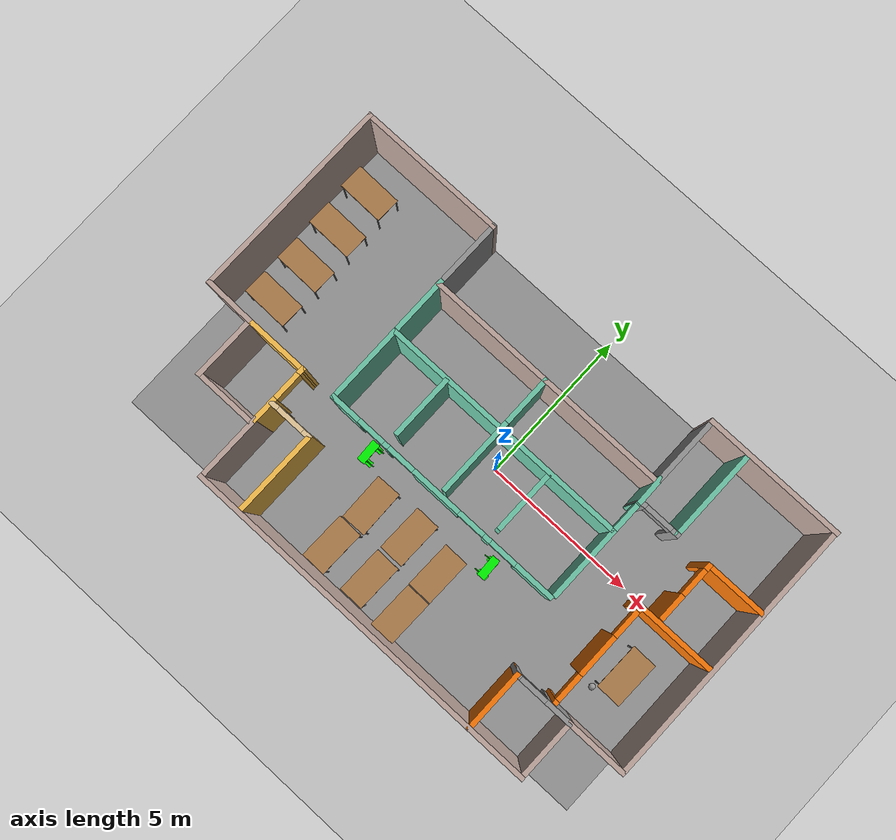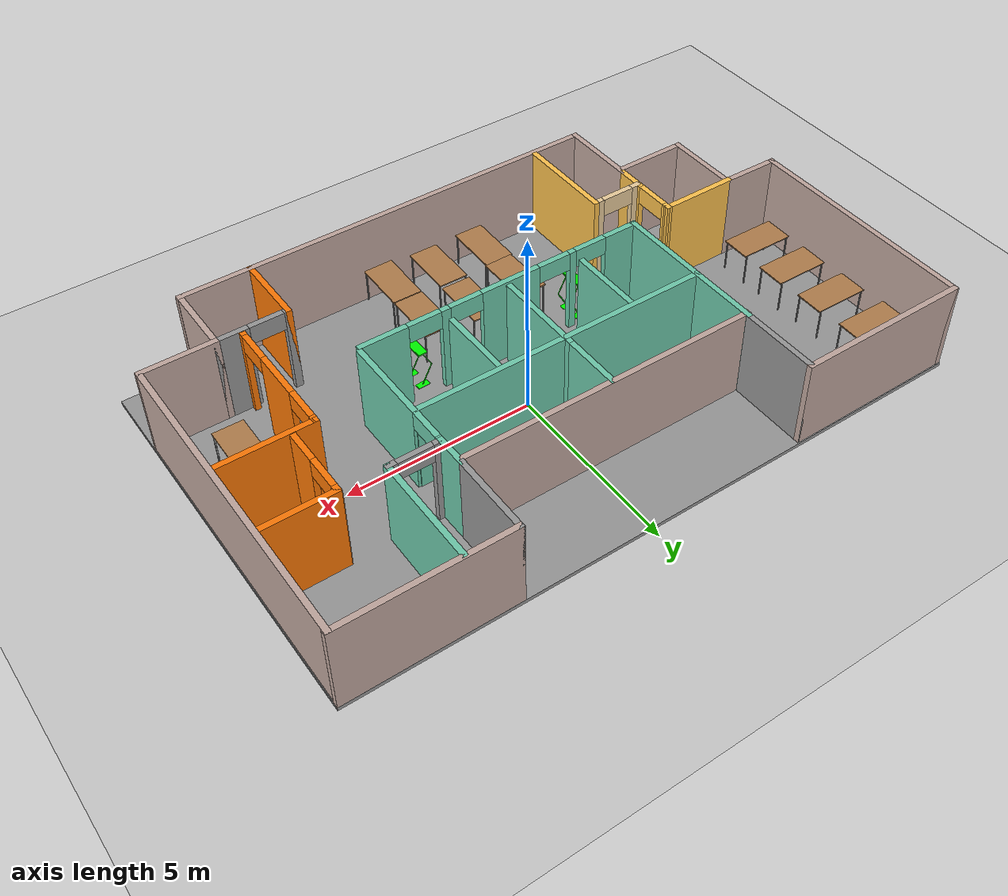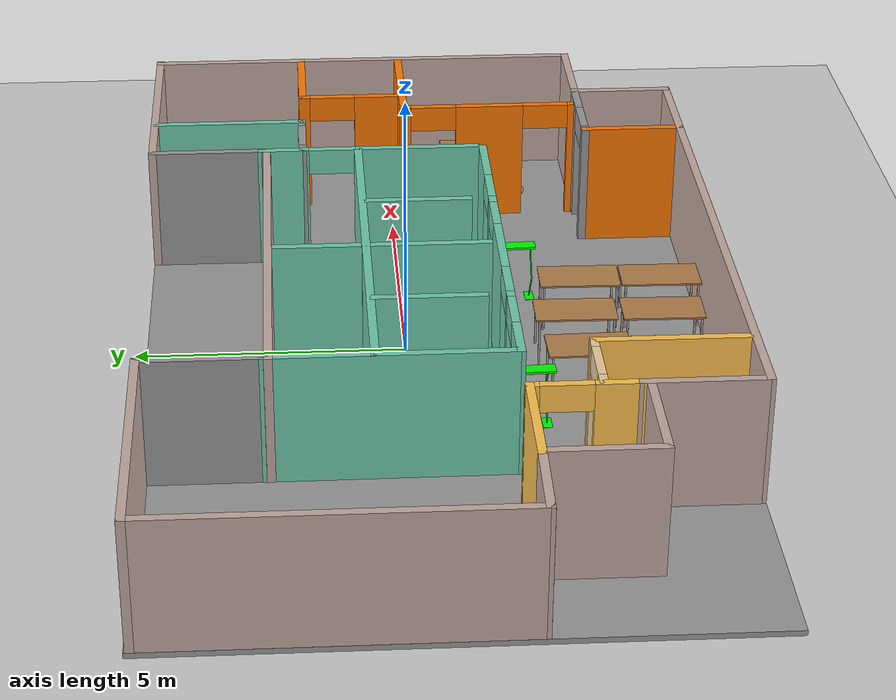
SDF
<sdf version="1.7">
 <world name="default">
  <plugin name="hello" filename="libhello.so"/>
  <gravity>0 0 -9.8</gravity>
  <magnetic_field>6e-06 2.3e-05 -4.2e-05</magnetic_field>
  <atmosphere type="adiabatic"/>
  <physics type="ode">
   <max_step_size>0.001</max_step_size>
   <real_time_factor>1</real_time_factor>
   <real_time_update_rate>1000</real_time_update_rate>
  </physics>
  <scene><ambient>0.4 0.4 0.4 1</ambient><background>0.7 0.7 0.7 1</background><shadows>1</shadows></scene>
  <spherical_coordinates>
   <surface_model>EARTH_WGS84</surface_model>
   <latitude_deg>0</latitude_deg>
   <longitude_deg>0</longitude_deg>
   <elevation>0</elevation>
   <heading_deg>0</heading_deg>
  </spherical_coordinates>
  <model name="Udacity_Office">
   <pose>-0.57091 -0.462357 0 0 -0 0</pose>
   <link name="Floor_0">
    <collision name="Floor_0_Collision">
     <geometry><box><size>17.0626 10.4763 0.1</size></box></geometry>
     <pose>0 0 0.05 0 -0 0</pose>
    </collision>
    <visual name="Floor_0_Visual">
     <pose>0 0 0.05 0 -0 0</pose>
     <geometry><box><size>17.0626 10.4763 0.1</size></box></geometry>
     <material>
      <script><uri>file://media/materials/scripts/gazebo.material</uri><name>Gazebo/Grey</name></script>
      <ambient>1 1 1 1</ambient>
     </material>
     <meta><layer>0</layer></meta>
    </visual>
   </link>
   <link name="Wall_113">
    <pose>-4.25156 -2.45124 0 0 -0 3.14159</pose>
    <visual name="Wall_113_Visual_0">
     <pose>-0.592857 0 1.25 0 -0 0</pose>
     <geometry><box><size>0.314286 0.15 2.5</size></box></geometry>
     <material>
      <script><uri>file://media/materials/scripts/gazebo.material</uri><name>Gazebo/Grey</name></script>
      <ambient>0.921569 0.807843 0.615686 1</ambient>
     </material>
     <meta><layer>0</layer></meta>
    </visual>
    <collision name="Wall_113_Collision_0">
     <geometry><box><size>0.314286 0.15 2.5</size></box></geometry>
     <pose>-0.592857 0 1.25 0 -0 0</pose>
    </collision>
    <visual name="Wall_113_Visual_1">
     <pose>0.607143 0 1.25 0 -0 0</pose>
     <geometry><box><size>0.285714 0.15 2.5</size></box></geometry>
     <material>
      <script><uri>file://media/materials/scripts/gazebo.material</uri><name>Gazebo/Grey</name></script>
      <ambient>0.921569 0.807843 0.615686 1</ambient>
     </material>
     <meta><layer>0</layer></meta>
    </visual>
    <collision name="Wall_113_Collision_1">
     <geometry><box><size>0.285714 0.15 2.5</size></box></geometry>
     <pose>0.607143 0 1.25 0 -0 0</pose>
    </collision>
    <visual name="Wall_113_Visual_2">
     <pose>0.014286 0 2.25 0 -0 0</pose>
     <geometry><box><size>0.9 0.15 0.5</size></box></geometry>
     <material>
      <script><uri>file://media/materials/scripts/gazebo.material</uri><name>Gazebo/Grey</name></script>
      <ambient>0.921569 0.807843 0.615686 1</ambient>
     </material>
     <meta><layer>0</layer></meta>
    </visual>
    <collision name="Wall_113_Collision_2">
     <geometry><box><size>0.9 0.15 0.5</size></box></geometry>
     <pose>0.014286 0 2.25 0 -0 0</pose>
    </collision>
   </link>
   <link name="Wall_13">
    <collision name="Wall_13_Collision">
     <geometry><box><size>11.7 0.15 2.5</size></box></geometry>
     <pose>0 0 1.25 0 -0 0</pose>
    </collision>
    <visual name="Wall_13_Visual">
     <pose>0 0 1.25 0 -0 0</pose>
     <geometry><box><size>11.7 0.15 2.5</size></box></geometry>
     <material>
      <script><uri>file://media/materials/scripts/gazebo.material</uri><name>Gazebo/Grey</name></script>
      <ambient>0.760784 0.662745 0.627451 1</ambient>
     </material>
     <meta><layer>0</layer></meta>
    </visual>
    <pose>0.81591 -5.16264 0 0 -0 0</pose>
   </link>
   <link name="Wall_16">
    <collision name="Wall_16_Collision">
     <geometry><box><size>8.5 0.15 2.5</size></box></geometry>
     <pose>0 0 1.25 0 -0 0</pose>
    </collision>
    <visual name="Wall_16_Visual">
     <pose>0 0 1.25 0 -0 0</pose>
     <geometry><box><size>8.5 0.15 2.5</size></box></geometry>
     <material>
      <script><uri>file://media/materials/scripts/gazebo.material</uri><name>Gazebo/Grey</name></script>
      <ambient>0.760784 0.662745 0.627451 1</ambient>
     </material>
     <meta><layer>0</layer></meta>
    </visual>
    <pose>8.4387 0.987797 0 0 -0 1.5708</pose>
   </link>
   <link name="Wall_202">
    <pose>5.66133 -3.29505 0 0 -0 0</pose>
    <visual name="Wall_202_Visual_0">
     <pose>-0.901413 0 1.25 0 -0 0</pose>
     <geometry><box><size>0.197175 0.15 2.5</size></box></geometry>
     <material>
      <script><uri>file://media/materials/scripts/gazebo.material</uri><name>Gazebo/Grey</name></script>
      <ambient>1 1 1 1</ambient>
     </material>
     <meta><layer>0</layer></meta>
    </visual>
    <collision name="Wall_202_Collision_0">
     <geometry><box><size>0.197175 0.15 2.5</size></box></geometry>
     <pose>-0.901413 0 1.25 0 -0 0</pose>
    </collision>
    <visual name="Wall_202_Visual_1">
     <pose>0.548587 0 1.25 0 -0 0</pose>
     <geometry><box><size>0.902825 0.15 2.5</size></box></geometry>
     <material>
      <script><uri>file://media/materials/scripts/gazebo.material</uri><name>Gazebo/Grey</name></script>
      <ambient>1 1 1 1</ambient>
     </material>
     <meta><layer>0</layer></meta>
    </visual>
    <collision name="Wall_202_Collision_1">
     <geometry><box><size>0.902825 0.15 2.5</size></box></geometry>
     <pose>0.548587 0 1.25 0 -0 0</pose>
    </collision>
    <visual name="Wall_202_Visual_2">
     <pose>-0.352825 0 2.25 0 -0 0</pose>
     <geometry><box><size>0.9 0.15 0.5</size></box></geometry>
     <material>
      <script><uri>file://media/materials/scripts/gazebo.material</uri><name>Gazebo/Grey</name></script>
      <ambient>1 1 1 1</ambient>
     </material>
     <meta><layer>0</layer></meta>
    </visual>
    <collision name="Wall_202_Collision_2">
     <geometry><box><size>0.9 0.15 0.5</size></box></geometry>
     <pose>-0.352825 0 2.25 0 -0 0</pose>
    </collision>
   </link>
   <link name="Wall_204">
    <collision name="Wall_204_Collision">
     <geometry><box><size>2.25 0.15 2.5</size></box></geometry>
     <pose>0 0 1.25 0 -0 0</pose>
    </collision>
    <visual name="Wall_204_Visual">
     <pose>0 0 1.25 0 -0 0</pose>
     <geometry><box><size>2.25 0.15 2.5</size></box></geometry>
     <material>
      <script><uri>file://media/materials/scripts/gazebo.material</uri><name>Gazebo/Grey</name></script>
      <ambient>1 1 1 1</ambient>
     </material>
     <meta><layer>0</layer></meta>
    </visual>
    <pose>4.07111 4.1128 0 0 -0 -1.5708</pose>
   </link>
   <link name="Wall_205">
    <collision name="Wall_205_Collision">
     <geometry><box><size>0.943544 0.15 2.5</size></box></geometry>
     <pose>0 0 1.25 0 -0 0</pose>
    </collision>
    <visual name="Wall_205_Visual">
     <pose>0 0 1.25 0 -0 0</pose>
     <geometry><box><size>0.943544 0.15 2.5</size></box></geometry>
     <material>
      <script><uri>file://media/materials/scripts/gazebo.material</uri><name>Gazebo/Grey</name></script>
      <ambient>0.435294 0.796078 0.67451 1</ambient>
     </material>
     <meta><layer>0</layer></meta>
    </visual>
    <pose>4.07751 2.66608 0 0 -0 -1.55467</pose>
   </link>
   <link name="Wall_206">
    <pose>4.08391 0.594357 0 0 -0 -1.5708</pose>
    <visual name="Wall_206_Visual_0">
     <pose>-1.65307 0 1.25 0 -0 0</pose>
     <geometry><box><size>0.193856 0.15 2.5</size></box></geometry>
     <material>
      <script><uri>file://media/materials/scripts/gazebo.material</uri><name>Gazebo/Grey</name></script>
      <ambient>0.435294 0.796078 0.67451 1</ambient>
     </material>
     <meta><layer>0</layer></meta>
    </visual>
    <collision name="Wall_206_Collision_0">
     <geometry><box><size>0.193856 0.15 2.5</size></box></geometry>
     <pose>-1.65307 0 1.25 0 -0 0</pose>
    </collision>
    <visual name="Wall_206_Visual_1">
     <pose>0.546928 0 1.25 0 -0 0</pose>
     <geometry><box><size>2.40614 0.15 2.5</size></box></geometry>
     <material>
      <script><uri>file://media/materials/scripts/gazebo.material</uri><name>Gazebo/Grey</name></script>
      <ambient>0.435294 0.796078 0.67451 1</ambient>
     </material>
     <meta><layer>0</layer></meta>
    </visual>
    <collision name="Wall_206_Collision_1">
     <geometry><box><size>2.40614 0.15 2.5</size></box></geometry>
     <pose>0.546928 0 1.25 0 -0 0</pose>
    </collision>
    <visual name="Wall_206_Visual_2">
     <pose>-1.10614 0 2.25 0 -0 0</pose>
     <geometry><box><size>0.9 0.15 0.5</size></box></geometry>
     <material>
      <script><uri>file://media/materials/scripts/gazebo.material</uri><name>Gazebo/Grey</name></script>
      <ambient>0.435294 0.796078 0.67451 1</ambient>
     </material>
     <meta><layer>0</layer></meta>
    </visual>
    <collision name="Wall_206_Collision_2">
     <geometry><box><size>0.9 0.15 0.5</size></box></geometry>
     <pose>-1.10614 0 2.25 0 -0 0</pose>
    </collision>
   </link>
   <link name="Wall_210">
    <collision name="Wall_210_Collision">
     <geometry><box><size>1.75 0.15 2.5</size></box></geometry>
     <pose>0 0 1.25 0 -0 0</pose>
    </collision>
    <visual name="Wall_210_Visual">
     <pose>0 0 1.25 0 -0 0</pose>
     <geometry><box><size>1.75 0.15 2.5</size></box></geometry>
     <material>
      <script><uri>file://media/materials/scripts/gazebo.material</uri><name>Gazebo/Grey</name></script>
      <ambient>0.435294 0.796078 0.67451 1</ambient>
     </material>
     <meta><layer>0</layer></meta>
    </visual>
    <pose>0.039901 2.15381 0 0 -0 -1.5708</pose>
   </link>
   <link name="Wall_211">
    <collision name="Wall_211_Collision">
     <geometry><box><size>2.5 0.15 2.5</size></box></geometry>
     <pose>0 0 1.25 0 -0 0</pose>
    </collision>
    <visual name="Wall_211_Visual">
     <pose>0 0 1.25 0 -0 0</pose>
     <geometry><box><size>2.5 0.15 2.5</size></box></geometry>
     <material>
      <script><uri>file://media/materials/scripts/gazebo.material</uri><name>Gazebo/Grey</name></script>
      <ambient>0.435294 0.796078 0.67451 1</ambient>
     </material>
     <meta><layer>0</layer></meta>
    </visual>
    <pose>0.039901 0.178808 0 0 -0 -1.5708</pose>
   </link>
   <link name="Wall_24">
    <pose>0.085541 -1.21442 0 0 -0 3.14159</pose>
    <visual name="Wall_24_Visual_0">
     <pose>-3.34594 0 1.25 0 -0 0</pose>
     <geometry><box><size>1.30812 0.15 2.5</size></box></geometry>
     <material>
      <script><uri>file://media/materials/scripts/gazebo.material</uri><name>Gazebo/Grey</name></script>
      <ambient>0.435294 0.796078 0.67451 1</ambient>
     </material>
     <meta><layer>0</layer></meta>
    </visual>
    <collision name="Wall_24_Collision_0">
     <geometry><box><size>1.30812 0.15 2.5</size></box></geometry>
     <pose>-3.34594 0 1.25 0 -0 0</pose>
    </collision>
    <visual name="Wall_24_Visual_1">
     <pose>-1.66844 0 1.25 0 -0 0</pose>
     <geometry><box><size>0.246882 0.15 2.5</size></box></geometry>
     <material>
      <script><uri>file://media/materials/scripts/gazebo.material</uri><name>Gazebo/Grey</name></script>
      <ambient>0.435294 0.796078 0.67451 1</ambient>
     </material>
     <meta><layer>0</layer></meta>
    </visual>
    <collision name="Wall_24_Collision_1">
     <geometry><box><size>0.246882 0.15 2.5</size></box></geometry>
     <pose>-1.66844 0 1.25 0 -0 0</pose>
    </collision>
    <visual name="Wall_24_Visual_2">
     <pose>0.17934 0 1.25 0 -0 0</pose>
     <geometry><box><size>1.64868 0.15 2.5</size></box></geometry>
     <material>
      <script><uri>file://media/materials/scripts/gazebo.material</uri><name>Gazebo/Grey</name></script>
      <ambient>0.435294 0.796078 0.67451 1</ambient>
     </material>
     <meta><layer>0</layer></meta>
    </visual>
    <collision name="Wall_24_Collision_2">
     <geometry><box><size>1.64868 0.15 2.5</size></box></geometry>
     <pose>0.17934 0 1.25 0 -0 0</pose>
    </collision>
    <visual name="Wall_24_Visual_3">
     <pose>1.99816 0 1.25 0 -0 0</pose>
     <geometry><box><size>0.188949 0.15 2.5</size></box></geometry>
     <material>
      <script><uri>file://media/materials/scripts/gazebo.material</uri><name>Gazebo/Grey</name></script>
      <ambient>0.435294 0.796078 0.67451 1</ambient>
     </material>
     <meta><layer>0</layer></meta>
    </visual>
    <collision name="Wall_24_Collision_3">
     <geometry><box><size>0.188949 0.15 2.5</size></box></geometry>
     <pose>1.99816 0 1.25 0 -0 0</pose>
    </collision>
    <visual name="Wall_24_Visual_4">
     <pose>3.49632 0 1.25 0 -0 0</pose>
     <geometry><box><size>1.00737 0.15 2.5</size></box></geometry>
     <material>
      <script><uri>file://media/materials/scripts/gazebo.material</uri><name>Gazebo/Grey</name></script>
      <ambient>0.435294 0.796078 0.67451 1</ambient>
     </material>
     <meta><layer>0</layer></meta>
    </visual>
    <collision name="Wall_24_Collision_4">
     <geometry><box><size>1.00737 0.15 2.5</size></box></geometry>
     <pose>3.49632 0 1.25 0 -0 0</pose>
    </collision>
    <visual name="Wall_24_Visual_5">
     <pose>-2.24188 0 2.25 0 -0 0</pose>
     <geometry><box><size>0.9 0.15 0.5</size></box></geometry>
     <material>
      <script><uri>file://media/materials/scripts/gazebo.material</uri><name>Gazebo/Grey</name></script>
      <ambient>0.435294 0.796078 0.67451 1</ambient>
     </material>
     <meta><layer>0</layer></meta>
    </visual>
    <collision name="Wall_24_Collision_5">
     <geometry><box><size>0.9 0.15 0.5</size></box></geometry>
     <pose>-2.24188 0 2.25 0 -0 0</pose>
    </collision>
    <visual name="Wall_24_Visual_6">
     <pose>-1.095 0 2.25 0 -0 0</pose>
     <geometry><box><size>0.9 0.15 0.5</size></box></geometry>
     <material>
      <script><uri>file://media/materials/scripts/gazebo.material</uri><name>Gazebo/Grey</name></script>
      <ambient>0.435294 0.796078 0.67451 1</ambient>
     </material>
     <meta><layer>0</layer></meta>
    </visual>
    <collision name="Wall_24_Collision_6">
     <geometry><box><size>0.9 0.15 0.5</size></box></geometry>
     <pose>-1.095 0 2.25 0 -0 0</pose>
    </collision>
    <visual name="Wall_24_Visual_7">
     <pose>1.45368 0 2.25 0 -0 0</pose>
     <geometry><box><size>0.9 0.15 0.5</size></box></geometry>
     <material>
      <script><uri>file://media/materials/scripts/gazebo.material</uri><name>Gazebo/Grey</name></script>
      <ambient>0.435294 0.796078 0.67451 1</ambient>
     </material>
     <meta><layer>0</layer></meta>
    </visual>
    <collision name="Wall_24_Collision_7">
     <geometry><box><size>0.9 0.15 0.5</size></box></geometry>
     <pose>1.45368 0 2.25 0 -0 0</pose>
    </collision>
    <visual name="Wall_24_Visual_8">
     <pose>2.54263 0 2.25 0 -0 0</pose>
     <geometry><box><size>0.9 0.15 0.5</size></box></geometry>
     <material>
      <script><uri>file://media/materials/scripts/gazebo.material</uri><name>Gazebo/Grey</name></script>
      <ambient>0.435294 0.796078 0.67451 1</ambient>
     </material>
     <meta><layer>0</layer></meta>
    </visual>
    <collision name="Wall_24_Collision_8">
     <geometry><box><size>0.9 0.15 0.5</size></box></geometry>
     <pose>2.54263 0 2.25 0 -0 0</pose>
    </collision>
   </link>
   <link name="Wall_30">
    <collision name="Wall_30_Collision">
     <geometry><box><size>2.04563 0.15 2.5</size></box></geometry>
     <pose>0 0 1.25 0 -0 0</pose>
    </collision>
    <visual name="Wall_30_Visual">
     <pose>0 0 1.25 0 -0 0</pose>
     <geometry><box><size>2.04563 0.15 2.5</size></box></geometry>
     <material>
      <script><uri>file://media/materials/scripts/gazebo.material</uri><name>Gazebo/Grey</name></script>
      <ambient>0.435294 0.796078 0.67451 1</ambient>
     </material>
     <meta><layer>0</layer></meta>
    </visual>
    <pose>-1.91909 0.184357 0 0 -0 -1.5708</pose>
   </link>
   <link name="Wall_36">
    <collision name="Wall_36_Collision">
     <geometry><box><size>2 0.15 2.5</size></box></geometry>
     <pose>0 0 1.25 0 -0 0</pose>
    </collision>
    <visual name="Wall_36_Visual">
     <pose>0 0 1.25 0 -0 0</pose>
     <geometry><box><size>2 0.15 2.5</size></box></geometry>
     <material>
      <script><uri>file://media/materials/scripts/gazebo.material</uri><name>Gazebo/Grey</name></script>
      <ambient>0.435294 0.796078 0.67451 1</ambient>
     </material>
     <meta><layer>0</layer></meta>
    </visual>
    <pose>1.81091 0.161357 0 0 -0 -1.5708</pose>
   </link>
   <link name="Wall_41">
    <collision name="Wall_41_Collision">
     <geometry><box><size>4.53518 0.15 2.5</size></box></geometry>
     <pose>0 0 1.25 0 -0 0</pose>
    </collision>
    <visual name="Wall_41_Visual">
     <pose>0 0 1.25 0 -0 0</pose>
     <geometry><box><size>4.53518 0.15 2.5</size></box></geometry>
     <material>
      <script><uri>file://media/materials/scripts/gazebo.material</uri><name>Gazebo/Grey</name></script>
      <ambient>0.760784 0.662745 0.627451 1</ambient>
     </material>
     <meta><layer>0</layer></meta>
    </visual>
    <pose>6.2637 5.1628 0 0 -0 0</pose>
   </link>
   <link name="Wall_43">
    <collision name="Wall_43_Collision">
     <geometry><box><size>8 0.15 2.5</size></box></geometry>
     <pose>0 0 1.25 0 -0 0</pose>
    </collision>
    <visual name="Wall_43_Visual">
     <pose>0 0 1.25 0 -0 0</pose>
     <geometry><box><size>8 0.15 2.5</size></box></geometry>
     <material>
      <script><uri>file://media/materials/scripts/gazebo.material</uri><name>Gazebo/Grey</name></script>
      <ambient>0.435294 0.796078 0.67451 1</ambient>
     </material>
     <meta><layer>0</layer></meta>
    </visual>
    <pose>0.083377 1.2008 0 0 -0 0</pose>
   </link>
   <link name="Wall_45">
    <collision name="Wall_45_Collision">
     <geometry><box><size>8 0.15 2.5</size></box></geometry>
     <pose>0 0 1.25 0 -0 0</pose>
    </collision>
    <visual name="Wall_45_Visual">
     <pose>0 0 1.25 0 -0 0</pose>
     <geometry><box><size>8 0.15 2.5</size></box></geometry>
     <material>
      <script><uri>file://media/materials/scripts/gazebo.material</uri><name>Gazebo/Grey</name></script>
      <ambient>0.760784 0.662745 0.627451 1</ambient>
     </material>
     <meta><layer>0</layer></meta>
    </visual>
    <pose>0.05634 2.96381 0 0 -0 0</pose>
   </link>
   <link name="Wall_50">
    <collision name="Wall_50_Collision">
     <geometry><box><size>2 0.15 2.5</size></box></geometry>
     <pose>0 0 1.25 0 -0 0</pose>
    </collision>
    <visual name="Wall_50_Visual">
     <pose>0 0 1.25 0 -0 0</pose>
     <geometry><box><size>2 0.15 2.5</size></box></geometry>
     <material>
      <script><uri>file://media/materials/scripts/gazebo.material</uri><name>Gazebo/Grey</name></script>
      <ambient>0.760784 0.662745 0.627451 1</ambient>
     </material>
     <meta><layer>0</layer></meta>
    </visual>
    <pose>-6.91954 -2.28121 0 0 -0 -1.5708</pose>
   </link>
   <link name="Wall_53">
    <collision name="Wall_53_Collision">
     <geometry><box><size>2 0.15 2.5</size></box></geometry>
     <pose>0 0 1.25 0 -0 0</pose>
    </collision>
    <visual name="Wall_53_Visual">
     <pose>0 0 1.25 0 -0 0</pose>
     <geometry><box><size>2 0.15 2.5</size></box></geometry>
     <material>
      <script><uri>file://media/materials/scripts/gazebo.material</uri><name>Gazebo/Grey</name></script>
      <ambient>0.760784 0.662745 0.627451 1</ambient>
     </material>
     <meta><layer>0</layer></meta>
    </visual>
    <pose>-5.99454 -3.20621 0 0 -0 0</pose>
   </link>
   <link name="Wall_61">
    <collision name="Wall_61_Collision">
     <geometry><box><size>4.75 0.15 2.5</size></box></geometry>
     <pose>0 0 1.25 0 -0 0</pose>
    </collision>
    <visual name="Wall_61_Visual">
     <pose>0 0 1.25 0 -0 0</pose>
     <geometry><box><size>4.75 0.15 2.5</size></box></geometry>
     <material>
      <script><uri>file://media/materials/scripts/gazebo.material</uri><name>Gazebo/Grey</name></script>
      <ambient>0.760784 0.662745 0.627451 1</ambient>
     </material>
     <meta><layer>0</layer></meta>
    </visual>
    <pose>-6.15493 5.13778 0 0 -0 0</pose>
   </link>
   <link name="Wall_63">
    <collision name="Wall_63_Collision">
     <geometry><box><size>2 0.15 2.5</size></box></geometry>
     <pose>0 0 1.25 0 -0 0</pose>
    </collision>
    <visual name="Wall_63_Visual">
     <pose>0 0 1.25 0 -0 0</pose>
     <geometry><box><size>2 0.15 2.5</size></box></geometry>
     <material>
      <script><uri>file://media/materials/scripts/gazebo.material</uri><name>Gazebo/Grey</name></script>
      <ambient>0.760784 0.662745 0.627451 1</ambient>
     </material>
     <meta><layer>0</layer></meta>
    </visual>
    <pose>7.51133 -3.29505 0 0 -0 0</pose>
   </link>
   <link name="Wall_68">
    <collision name="Wall_68_Collision">
     <geometry><box><size>2 0.15 2.5</size></box></geometry>
     <pose>0 0 1.25 0 -0 0</pose>
    </collision>
    <visual name="Wall_68_Visual">
     <pose>0 0 1.25 0 -0 0</pose>
     <geometry><box><size>2 0.15 2.5</size></box></geometry>
     <material>
      <script><uri>file://media/materials/scripts/gazebo.material</uri><name>Gazebo/Grey</name></script>
      <ambient>0.760784 0.662745 0.627451 1</ambient>
     </material>
     <meta><layer>0</layer></meta>
    </visual>
    <pose>6.58633 -4.22005 0 0 -0 -1.5708</pose>
   </link>
   <link name="Wall_71">
    <collision name="Wall_71_Collision">
     <geometry><box><size>2 0.15 2.5</size></box></geometry>
     <pose>0 0 1.25 0 -0 0</pose>
    </collision>
    <visual name="Wall_71_Visual">
     <pose>0 0 1.25 0 -0 0</pose>
     <geometry><box><size>2 0.15 2.5</size></box></geometry>
     <material>
      <script><uri>file://media/materials/scripts/gazebo.material</uri><name>Gazebo/Grey</name></script>
      <ambient>0.996078 0.47451 0.0196078 1</ambient>
     </material>
     <meta><layer>0</layer></meta>
    </visual>
    <pose>4.73633 -4.22005 0 0 -0 -1.5708</pose>
   </link>
   <link name="Wall_76">
    <pose>5.95517 -1.45473 0 0 -0 1.5708</pose>
    <visual name="Wall_76_Visual_0">
     <pose>-1.68721 0 1.25 0 -0 0</pose>
     <geometry><box><size>0.125574 0.15 2.5</size></box></geometry>
     <material>
      <script><uri>file://media/materials/scripts/gazebo.material</uri><name>Gazebo/Grey</name></script>
      <ambient>0.996078 0.47451 0.0196078 1</ambient>
     </material>
     <meta><layer>0</layer></meta>
    </visual>
    <collision name="Wall_76_Collision_0">
     <geometry><box><size>0.125574 0.15 2.5</size></box></geometry>
     <pose>-1.68721 0 1.25 0 -0 0</pose>
    </collision>
    <visual name="Wall_76_Visual_1">
     <pose>-0.04908 0 1.25 0 -0 0</pose>
     <geometry><box><size>1.35069 0.15 2.5</size></box></geometry>
     <material>
      <script><uri>file://media/materials/scripts/gazebo.material</uri><name>Gazebo/Grey</name></script>
      <ambient>0.996078 0.47451 0.0196078 1</ambient>
     </material>
     <meta><layer>0</layer></meta>
    </visual>
    <collision name="Wall_76_Collision_1">
     <geometry><box><size>1.35069 0.15 2.5</size></box></geometry>
     <pose>-0.04908 0 1.25 0 -0 0</pose>
    </collision>
    <visual name="Wall_76_Visual_2">
     <pose>1.63813 0 1.25 0 -0 0</pose>
     <geometry><box><size>0.223734 0.15 2.5</size></box></geometry>
     <material>
      <script><uri>file://media/materials/scripts/gazebo.material</uri><name>Gazebo/Grey</name></script>
      <ambient>0.996078 0.47451 0.0196078 1</ambient>
     </material>
     <meta><layer>0</layer></meta>
    </visual>
    <collision name="Wall_76_Collision_2">
     <geometry><box><size>0.223734 0.15 2.5</size></box></geometry>
     <pose>1.63813 0 1.25 0 -0 0</pose>
    </collision>
    <visual name="Wall_76_Visual_3">
     <pose>-1.17443 0 2.25 0 -0 0</pose>
     <geometry><box><size>0.9 0.15 0.5</size></box></geometry>
     <material>
      <script><uri>file://media/materials/scripts/gazebo.material</uri><name>Gazebo/Grey</name></script>
      <ambient>0.996078 0.47451 0.0196078 1</ambient>
     </material>
     <meta><layer>0</layer></meta>
    </visual>
    <collision name="Wall_76_Collision_3">
     <geometry><box><size>0.9 0.15 0.5</size></box></geometry>
     <pose>-1.17443 0 2.25 0 -0 0</pose>
    </collision>
    <visual name="Wall_76_Visual_4">
     <pose>1.07627 0 2.25 0 -0 0</pose>
     <geometry><box><size>0.9 0.15 0.5</size></box></geometry>
     <material>
      <script><uri>file://media/materials/scripts/gazebo.material</uri><name>Gazebo/Grey</name></script>
      <ambient>0.996078 0.47451 0.0196078 1</ambient>
     </material>
     <meta><layer>0</layer></meta>
    </visual>
    <collision name="Wall_76_Collision_4">
     <geometry><box><size>0.9 0.15 0.5</size></box></geometry>
     <pose>1.07627 0 2.25 0 -0 0</pose>
    </collision>
   </link>
   <link name="Wall_77">
    <collision name="Wall_77_Collision">
     <geometry><box><size>2.5 0.15 2.5</size></box></geometry>
     <pose>0 0 1.25 0 -0 0</pose>
    </collision>
    <visual name="Wall_77_Visual">
     <pose>0 0 1.25 0 -0 0</pose>
     <geometry><box><size>2.5 0.15 2.5</size></box></geometry>
     <material>
      <script><uri>file://media/materials/scripts/gazebo.material</uri><name>Gazebo/Grey</name></script>
      <ambient>0.996078 0.47451 0.0196078 1</ambient>
     </material>
     <meta><layer>0</layer></meta>
    </visual>
    <pose>7.13017 0.220269 0 0 -0 0</pose>
   </link>
   <link name="Wall_79">
    <pose>6.54993 1.31097 0 0 -0 1.5708</pose>
    <visual name="Wall_79_Visual_0">
     <pose>-0.561144 0 1.25 0 -0 0</pose>
     <geometry><box><size>0.877712 0.15 2.5</size></box></geometry>
     <material>
      <script><uri>file://media/materials/scripts/gazebo.material</uri><name>Gazebo/Grey</name></script>
      <ambient>0.996078 0.47451 0.0196078 1</ambient>
     </material>
     <meta><layer>0</layer></meta>
    </visual>
    <collision name="Wall_79_Collision_0">
     <geometry><box><size>0.877712 0.15 2.5</size></box></geometry>
     <pose>-0.561144 0 1.25 0 -0 0</pose>
    </collision>
    <visual name="Wall_79_Visual_1">
     <pose>0.888856 0 1.25 0 -0 0</pose>
     <geometry><box><size>0.222288 0.15 2.5</size></box></geometry>
     <material>
      <script><uri>file://media/materials/scripts/gazebo.material</uri><name>Gazebo/Grey</name></script>
      <ambient>0.996078 0.47451 0.0196078 1</ambient>
     </material>
     <meta><layer>0</layer></meta>
    </visual>
    <collision name="Wall_79_Collision_1">
     <geometry><box><size>0.222288 0.15 2.5</size></box></geometry>
     <pose>0.888856 0 1.25 0 -0 0</pose>
    </collision>
    <visual name="Wall_79_Visual_2">
     <pose>0.327712 0 2.25 0 -0 0</pose>
     <geometry><box><size>0.9 0.15 0.5</size></box></geometry>
     <material>
      <script><uri>file://media/materials/scripts/gazebo.material</uri><name>Gazebo/Grey</name></script>
      <ambient>0.996078 0.47451 0.0196078 1</ambient>
     </material>
     <meta><layer>0</layer></meta>
    </visual>
    <collision name="Wall_79_Collision_2">
     <geometry><box><size>0.9 0.15 0.5</size></box></geometry>
     <pose>0.327712 0 2.25 0 -0 0</pose>
    </collision>
   </link>
   <link name="Wall_80">
    <collision name="Wall_80_Collision">
     <geometry><box><size>1.95412 0.15 2.5</size></box></geometry>
     <pose>0 0 1.25 0 -0 0</pose>
    </collision>
    <visual name="Wall_80_Visual">
     <pose>0 0 1.25 0 -0 0</pose>
     <geometry><box><size>1.95412 0.15 2.5</size></box></geometry>
     <material>
      <script><uri>file://media/materials/scripts/gazebo.material</uri><name>Gazebo/Grey</name></script>
      <ambient>0.996078 0.47451 0.0196078 1</ambient>
     </material>
     <meta><layer>0</layer></meta>
    </visual>
    <pose>7.46728 2.23597 0 0 -0 0</pose>
   </link>
   <link name="Wall_84">
    <collision name="Wall_84_Collision">
     <geometry><box><size>3 0.15 2.5</size></box></geometry>
     <pose>0 0 1.25 0 -0 0</pose>
    </collision>
    <visual name="Wall_84_Visual">
     <pose>0 0 1.25 0 -0 0</pose>
     <geometry><box><size>3 0.15 2.5</size></box></geometry>
     <material>
      <script><uri>file://media/materials/scripts/gazebo.material</uri><name>Gazebo/Grey</name></script>
      <ambient>0.435294 0.796078 0.67451 1</ambient>
     </material>
     <meta><layer>0</layer></meta>
    </visual>
    <pose>5.38388 3.69451 0 0 -0 -1.57077</pose>
   </link>
   <link name="Wall_85">
    <pose>4.73391 2.26936 0 0 -0 3.14159</pose>
    <visual name="Wall_85_Visual_0">
     <pose>-0.590794 0 1.25 0 -0 0</pose>
     <geometry><box><size>0.268411 0.15 2.5</size></box></geometry>
     <material>
      <script><uri>file://media/materials/scripts/gazebo.material</uri><name>Gazebo/Grey</name></script>
      <ambient>1 1 1 1</ambient>
     </material>
     <meta><layer>0</layer></meta>
    </visual>
    <collision name="Wall_85_Collision_0">
     <geometry><box><size>0.268411 0.15 2.5</size></box></geometry>
     <pose>-0.590794 0 1.25 0 -0 0</pose>
    </collision>
    <visual name="Wall_85_Visual_1">
     <pose>0.584206 0 1.25 0 -0 0</pose>
     <geometry><box><size>0.281589 0.15 2.5</size></box></geometry>
     <material>
      <script><uri>file://media/materials/scripts/gazebo.material</uri><name>Gazebo/Grey</name></script>
      <ambient>1 1 1 1</ambient>
     </material>
     <meta><layer>0</layer></meta>
    </visual>
    <collision name="Wall_85_Collision_1">
     <geometry><box><size>0.281589 0.15 2.5</size></box></geometry>
     <pose>0.584206 0 1.25 0 -0 0</pose>
    </collision>
    <visual name="Wall_85_Visual_2">
     <pose>-0.006589 0 2.25 0 -0 0</pose>
     <geometry><box><size>0.9 0.15 0.5</size></box></geometry>
     <material>
      <script><uri>file://media/materials/scripts/gazebo.material</uri><name>Gazebo/Grey</name></script>
      <ambient>1 1 1 1</ambient>
     </material>
     <meta><layer>0</layer></meta>
    </visual>
    <collision name="Wall_85_Collision_2">
     <geometry><box><size>0.9 0.15 0.5</size></box></geometry>
     <pose>-0.006589 0 2.25 0 -0 0</pose>
    </collision>
   </link>
   <link name="Wall_87">
    <collision name="Wall_87_Collision">
     <geometry><box><size>2.75 0.15 2.5</size></box></geometry>
     <pose>0 0 1.25 0 -0 0</pose>
    </collision>
    <visual name="Wall_87_Visual">
     <pose>0 0 1.25 0 -0 0</pose>
     <geometry><box><size>2.75 0.15 2.5</size></box></geometry>
     <material>
      <script><uri>file://media/materials/scripts/gazebo.material</uri><name>Gazebo/Grey</name></script>
      <ambient>1 0.764706 0.305882 1</ambient>
     </material>
     <meta><layer>0</layer></meta>
    </visual>
    <pose>-3.57656 -3.75124 0 0 -0 -1.5708</pose>
   </link>
   <link name="Wall_89">
    <pose>-4.96337 -2.1642 0 0 -0 -1.5708</pose>
    <visual name="Wall_89_Visual_0">
     <pose>-0.882416 0 1.25 0 -0 0</pose>
     <geometry><box><size>0.235169 0.15 2.5</size></box></geometry>
     <material>
      <script><uri>file://media/materials/scripts/gazebo.material</uri><name>Gazebo/Grey</name></script>
      <ambient>1 0.764706 0.305882 1</ambient>
     </material>
     <meta><layer>0</layer></meta>
    </visual>
    <collision name="Wall_89_Collision_0">
     <geometry><box><size>0.235169 0.15 2.5</size></box></geometry>
     <pose>-0.882416 0 1.25 0 -0 0</pose>
    </collision>
    <visual name="Wall_89_Visual_1">
     <pose>0.567584 0 1.25 0 -0 0</pose>
     <geometry><box><size>0.864831 0.15 2.5</size></box></geometry>
     <material>
      <script><uri>file://media/materials/scripts/gazebo.material</uri><name>Gazebo/Grey</name></script>
      <ambient>1 0.764706 0.305882 1</ambient>
     </material>
     <meta><layer>0</layer></meta>
    </visual>
    <collision name="Wall_89_Collision_1">
     <geometry><box><size>0.864831 0.15 2.5</size></box></geometry>
     <pose>0.567584 0 1.25 0 -0 0</pose>
    </collision>
    <visual name="Wall_89_Visual_2">
     <pose>-0.314831 0 2.25 0 -0 0</pose>
     <geometry><box><size>0.9 0.15 0.5</size></box></geometry>
     <material>
      <script><uri>file://media/materials/scripts/gazebo.material</uri><name>Gazebo/Grey</name></script>
      <ambient>1 0.764706 0.305882 1</ambient>
     </material>
     <meta><layer>0</layer></meta>
    </visual>
    <collision name="Wall_89_Collision_2">
     <geometry><box><size>0.9 0.15 0.5</size></box></geometry>
     <pose>-0.314831 0 2.25 0 -0 0</pose>
    </collision>
   </link>
   <link name="Wall_9">
    <collision name="Wall_9_Collision">
     <geometry><box><size>6.5 0.15 2.5</size></box></geometry>
     <pose>0 0 1.25 0 -0 0</pose>
    </collision>
    <visual name="Wall_9_Visual">
     <pose>0 0 1.25 0 -0 0</pose>
     <geometry><box><size>6.5 0.15 2.5</size></box></geometry>
     <material>
      <script><uri>file://media/materials/scripts/gazebo.material</uri><name>Gazebo/Grey</name></script>
      <ambient>0.760784 0.662745 0.627451 1</ambient>
     </material>
     <meta><layer>0</layer></meta>
    </visual>
    <pose>-8.45493 1.96278 0 0 -0 -1.5708</pose>
   </link>
   <link name="Wall_90">
    <collision name="Wall_90_Collision">
     <geometry><box><size>2.22344 0.15 2.5</size></box></geometry>
     <pose>0 0 1.25 0 -0 0</pose>
    </collision>
    <visual name="Wall_90_Visual">
     <pose>0 0 1.25 0 -0 0</pose>
     <geometry><box><size>2.22344 0.15 2.5</size></box></geometry>
     <material>
      <script><uri>file://media/materials/scripts/gazebo.material</uri><name>Gazebo/Grey</name></script>
      <ambient>0.760784 0.662745 0.627451 1</ambient>
     </material>
     <meta><layer>0</layer></meta>
    </visual>
    <pose>-4.96123 -4.12592 0 0 -0 -1.56873</pose>
   </link>
   <link name="Wall_93">
    <collision name="Wall_93_Collision">
     <geometry><box><size>2.14972 0.15 2.5</size></box></geometry>
     <pose>0 0 1.25 0 -0 0</pose>
    </collision>
    <visual name="Wall_93_Visual">
     <pose>0 0 1.25 0 -0 0</pose>
     <geometry><box><size>2.14972 0.15 2.5</size></box></geometry>
     <material>
      <script><uri>file://media/materials/scripts/gazebo.material</uri><name>Gazebo/Grey</name></script>
      <ambient>1 0.764706 0.305882 1</ambient>
     </material>
     <meta><layer>0</layer></meta>
    </visual>
    <pose>-5.96323 -1.23942 0 0 -0 0.00022</pose>
   </link>
   <link name="Wall_95">
    <collision name="Wall_95_Collision">
     <geometry><box><size>4.4022 0.15 2.5</size></box></geometry>
     <pose>0 0 1.25 0 -0 0</pose>
    </collision>
    <visual name="Wall_95_Visual">
     <pose>0 0 1.25 0 -0 0</pose>
     <geometry><box><size>4.4022 0.15 2.5</size></box></geometry>
     <material>
      <script><uri>file://media/materials/scripts/gazebo.material</uri><name>Gazebo/Grey</name></script>
      <ambient>0.435294 0.796078 0.67451 1</ambient>
     </material>
     <meta><layer>0</layer></meta>
    </visual>
    <pose>-3.84719 0.911682 0 0 -0 1.57443</pose>
   </link>
   <link name="Wall_96">
    <collision name="Wall_96_Collision">
     <geometry><box><size>2.25 0.15 2.5</size></box></geometry>
     <pose>0 0 1.25 0 -0 0</pose>
    </collision>
    <visual name="Wall_96_Visual">
     <pose>0 0 1.25 0 -0 0</pose>
     <geometry><box><size>2.25 0.15 2.5</size></box></geometry>
     <material>
      <script><uri>file://media/materials/scripts/gazebo.material</uri><name>Gazebo/Grey</name></script>
      <ambient>1 1 1 1</ambient>
     </material>
     <meta><layer>0</layer></meta>
    </visual>
    <pose>-3.85493 4.08778 0 0 -0 1.5708</pose>
   </link>
   <link name="Wall_99">
    <collision name="Wall_99_Collision">
     <geometry><box><size>1.64209 0.15 2.5</size></box></geometry>
     <pose>0 0 1.25 0 -0 0</pose>
    </collision>
    <visual name="Wall_99_Visual">
     <pose>0 0 1.25 0 -0 0</pose>
     <geometry><box><size>1.64209 0.15 2.5</size></box></geometry>
     <material>
      <script><uri>file://media/materials/scripts/gazebo.material</uri><name>Gazebo/Grey</name></script>
      <ambient>0.760784 0.662745 0.627451 1</ambient>
     </material>
     <meta><layer>0</layer></meta>
    </visual>
    <pose>-7.70901 -1.22593 0 0 -0 -0.018382</pose>
   </link>
   <static>1</static>
  </model>
  <light name="user_spot_light_0" type="spot">
   <pose>-8.88468 17.3431 1 0 -0 0</pose>
   <diffuse>0.5 0.5 0.5 1</diffuse>
   <specular>0.1 0.1 0.1 1</specular>
   <direction>0 0 -1</direction>
   <attenuation>
    <range>20</range>
    <constant>0.5</constant>
    <linear>0.01</linear>
    <quadratic>0.001</quadratic>
   </attenuation>
   <cast_shadows>0</cast_shadows>
   <spot><inner_angle>0.6</inner_angle><outer_angle>1</outer_angle><falloff>1</falloff></spot>
  </light>
  <light name="sun" type="directional">
   <pose>8.26754 3.40508 10 0 -0 0</pose>
   <diffuse>0.8 0.8 0.8 1</diffuse>
   <specular>0.2 0.2 0.2 1</specular>
   <attenuation>
    <range>1000</range>
    <constant>0.9</constant>
    <linear>0.01</linear>
    <quadratic>0.001</quadratic>
   </attenuation>
   <direction>-0.5 0.1 -0.9</direction>
   <spot><inner_angle>0</inner_angle><outer_angle>0</outer_angle><falloff>0</falloff></spot>
  </light>
  <model name="table">
   <static>1</static>
   <link name="link">
    <collision name="surface">
     <pose>0 0 1 0 -0 0</pose>
     <geometry><box><size>1.5 0.8 0.03</size></box></geometry>
     <surface><friction><ode><mu>0.6</mu><mu2>0.6</mu2></ode></friction></surface>
    </collision>
    <visual name="visual1">
     <pose>0 0 1 0 -0 0</pose>
     <geometry><box><size>1.5 0.8 0.03</size></box></geometry>
     <material>
      <script><uri>file://media/materials/scripts/gazebo.material</uri><name>Gazebo/Wood</name></script>
     </material>
    </visual>
    <collision name="front_left_leg">
     <pose>0.68 0.38 0.5 0 -0 0</pose>
     <geometry><cylinder><radius>0.02</radius><length>1</length></cylinder></geometry>
    </collision>
    <visual name="front_left_leg">
     <pose>0.68 0.38 0.5 0 -0 0</pose>
     <geometry><cylinder><radius>0.02</radius><length>1</length></cylinder></geometry>
     <material>
      <script><uri>file://media/materials/scripts/gazebo.material</uri><name>Gazebo/Grey</name></script>
     </material>
    </visual>
    <collision name="front_right_leg">
     <pose>0.68 -0.38 0.5 0 -0 0</pose>
     <geometry><cylinder><radius>0.02</radius><length>1</length></cylinder></geometry>
    </collision>
    <visual name="front_right_leg">
     <pose>0.68 -0.38 0.5 0 -0 0</pose>
     <geometry><cylinder><radius>0.02</radius><length>1</length></cylinder></geometry>
     <material>
      <script><uri>file://media/materials/scripts/gazebo.material</uri><name>Gazebo/Grey</name></script>
     </material>
    </visual>
    <collision name="back_right_leg">
     <pose>-0.68 -0.38 0.5 0 -0 0</pose>
     <geometry><cylinder><radius>0.02</radius><length>1</length></cylinder></geometry>
    </collision>
    <visual name="back_right_leg">
     <pose>-0.68 -0.38 0.5 0 -0 0</pose>
     <geometry><cylinder><radius>0.02</radius><length>1</length></cylinder></geometry>
     <material>
      <script><uri>file://media/materials/scripts/gazebo.material</uri><name>Gazebo/Grey</name></script>
     </material>
    </visual>
    <collision name="back_left_leg">
     <pose>-0.68 0.38 0.5 0 -0 0</pose>
     <geometry><cylinder><radius>0.02</radius><length>1</length></cylinder></geometry>
    </collision>
    <visual name="back_left_leg">
     <pose>-0.68 0.38 0.5 0 -0 0</pose>
     <geometry><cylinder><radius>0.02</radius><length>1</length></cylinder></geometry>
     <material>
      <script><uri>file://media/materials/scripts/gazebo.material</uri><name>Gazebo/Grey</name></script>
     </material>
    </visual>
   </link>
   <pose>-1.82507 -3.1573 0.0487 0 0 -1.55059</pose>
  </model>
  <model name="table_clone">
   <static>1</static>
   <link name="link">
    <collision name="surface">
     <pose>0 0 1 0 -0 0</pose>
     <geometry><box><size>1.5 0.8 0.03</size></box></geometry>
     <surface><friction><ode><mu>0.6</mu><mu2>0.6</mu2></ode></friction></surface>
    </collision>
    <visual name="visual1">
     <pose>0 0 1 0 -0 0</pose>
     <geometry><box><size>1.5 0.8 0.03</size></box></geometry>
     <material>
      <script><uri>file://media/materials/scripts/gazebo.material</uri><name>Gazebo/Wood</name></script>
     </material>
    </visual>
    <collision name="front_left_leg">
     <pose>0.68 0.38 0.5 0 -0 0</pose>
     <geometry><cylinder><radius>0.02</radius><length>1</length></cylinder></geometry>
    </collision>
    <visual name="front_left_leg">
     <pose>0.68 0.38 0.5 0 -0 0</pose>
     <geometry><cylinder><radius>0.02</radius><length>1</length></cylinder></geometry>
     <material>
      <script><uri>file://media/materials/scripts/gazebo.material</uri><name>Gazebo/Grey</name></script>
     </material>
    </visual>
    <collision name="front_right_leg">
     <pose>0.68 -0.38 0.5 0 -0 0</pose>
     <geometry><cylinder><radius>0.02</radius><length>1</length></cylinder></geometry>
    </collision>
    <visual name="front_right_leg">
     <pose>0.68 -0.38 0.5 0 -0 0</pose>
     <geometry><cylinder><radius>0.02</radius><length>1</length></cylinder></geometry>
     <material>
      <script><uri>file://media/materials/scripts/gazebo.material</uri><name>Gazebo/Grey</name></script>
     </material>
    </visual>
    <collision name="back_right_leg">
     <pose>-0.68 -0.38 0.5 0 -0 0</pose>
     <geometry><cylinder><radius>0.02</radius><length>1</length></cylinder></geometry>
    </collision>
    <visual name="back_right_leg">
     <pose>-0.68 -0.38 0.5 0 -0 0</pose>
     <geometry><cylinder><radius>0.02</radius><length>1</length></cylinder></geometry>
     <material>
      <script><uri>file://media/materials/scripts/gazebo.material</uri><name>Gazebo/Grey</name></script>
     </material>
    </visual>
    <collision name="back_left_leg">
     <pose>-0.68 0.38 0.5 0 -0 0</pose>
     <geometry><cylinder><radius>0.02</radius><length>1</length></cylinder></geometry>
    </collision>
    <visual name="back_left_leg">
     <pose>-0.68 0.38 0.5 0 -0 0</pose>
     <geometry><cylinder><radius>0.02</radius><length>1</length></cylinder></geometry>
     <material>
      <script><uri>file://media/materials/scripts/gazebo.material</uri><name>Gazebo/Grey</name></script>
     </material>
    </visual>
   </link>
   <pose>-1.89111 -4.70011 0 0 0 -1.58492</pose>
  </model>
  <model name="table_clone_0">
   <static>1</static>
   <link name="link">
    <collision name="surface">
     <pose>0 0 1 0 -0 0</pose>
     <geometry><box><size>1.5 0.8 0.03</size></box></geometry>
     <surface><friction><ode><mu>0.6</mu><mu2>0.6</mu2></ode></friction></surface>
    </collision>
    <visual name="visual1">
     <pose>0 0 1 0 -0 0</pose>
     <geometry><box><size>1.5 0.8 0.03</size></box></geometry>
     <material>
      <script><uri>file://media/materials/scripts/gazebo.material</uri><name>Gazebo/Wood</name></script>
     </material>
    </visual>
    <collision name="front_left_leg">
     <pose>0.68 0.38 0.5 0 -0 0</pose>
     <geometry><cylinder><radius>0.02</radius><length>1</length></cylinder></geometry>
    </collision>
    <visual name="front_left_leg">
     <pose>0.68 0.38 0.5 0 -0 0</pose>
     <geometry><cylinder><radius>0.02</radius><length>1</length></cylinder></geometry>
     <material>
      <script><uri>file://media/materials/scripts/gazebo.material</uri><name>Gazebo/Grey</name></script>
     </material>
    </visual>
    <collision name="front_right_leg">
     <pose>0.68 -0.38 0.5 0 -0 0</pose>
     <geometry><cylinder><radius>0.02</radius><length>1</length></cylinder></geometry>
    </collision>
    <visual name="front_right_leg">
     <pose>0.68 -0.38 0.5 0 -0 0</pose>
     <geometry><cylinder><radius>0.02</radius><length>1</length></cylinder></geometry>
     <material>
      <script><uri>file://media/materials/scripts/gazebo.material</uri><name>Gazebo/Grey</name></script>
     </material>
    </visual>
    <collision name="back_right_leg">
     <pose>-0.68 -0.38 0.5 0 -0 0</pose>
     <geometry><cylinder><radius>0.02</radius><length>1</length></cylinder></geometry>
    </collision>
    <visual name="back_right_leg">
     <pose>-0.68 -0.38 0.5 0 -0 0</pose>
     <geometry><cylinder><radius>0.02</radius><length>1</length></cylinder></geometry>
     <material>
      <script><uri>file://media/materials/scripts/gazebo.material</uri><name>Gazebo/Grey</name></script>
     </material>
    </visual>
    <collision name="back_left_leg">
     <pose>-0.68 0.38 0.5 0 -0 0</pose>
     <geometry><cylinder><radius>0.02</radius><length>1</length></cylinder></geometry>
    </collision>
    <visual name="back_left_leg">
     <pose>-0.68 0.38 0.5 0 -0 0</pose>
     <geometry><cylinder><radius>0.02</radius><length>1</length></cylinder></geometry>
     <material>
      <script><uri>file://media/materials/scripts/gazebo.material</uri><name>Gazebo/Grey</name></script>
     </material>
    </visual>
   </link>
   <pose>-0.472288 -4.67796 0 0 0 -1.58492</pose>
  </model>
  <model name="table_clone_1">
   <static>1</static>
   <link name="link">
    <collision name="surface">
     <pose>0 0 1 0 -0 0</pose>
     <geometry><box><size>1.5 0.8 0.03</size></box></geometry>
     <surface><friction><ode><mu>0.6</mu><mu2>0.6</mu2></ode></friction></surface>
    </collision>
    <visual name="visual1">
     <pose>0 0 1 0 -0 0</pose>
     <geometry><box><size>1.5 0.8 0.03</size></box></geometry>
     <material>
      <script><uri>file://media/materials/scripts/gazebo.material</uri><name>Gazebo/Wood</name></script>
     </material>
    </visual>
    <collision name="front_left_leg">
     <pose>0.68 0.38 0.5 0 -0 0</pose>
     <geometry><cylinder><radius>0.02</radius><length>1</length></cylinder></geometry>
    </collision>
    <visual name="front_left_leg">
     <pose>0.68 0.38 0.5 0 -0 0</pose>
     <geometry><cylinder><radius>0.02</radius><length>1</length></cylinder></geometry>
     <material>
      <script><uri>file://media/materials/scripts/gazebo.material</uri><name>Gazebo/Grey</name></script>
     </material>
    </visual>
    <collision name="front_right_leg">
     <pose>0.68 -0.38 0.5 0 -0 0</pose>
     <geometry><cylinder><radius>0.02</radius><length>1</length></cylinder></geometry>
    </collision>
    <visual name="front_right_leg">
     <pose>0.68 -0.38 0.5 0 -0 0</pose>
     <geometry><cylinder><radius>0.02</radius><length>1</length></cylinder></geometry>
     <material>
      <script><uri>file://media/materials/scripts/gazebo.material</uri><name>Gazebo/Grey</name></script>
     </material>
    </visual>
    <collision name="back_right_leg">
     <pose>-0.68 -0.38 0.5 0 -0 0</pose>
     <geometry><cylinder><radius>0.02</radius><length>1</length></cylinder></geometry>
    </collision>
    <visual name="back_right_leg">
     <pose>-0.68 -0.38 0.5 0 -0 0</pose>
     <geometry><cylinder><radius>0.02</radius><length>1</length></cylinder></geometry>
     <material>
      <script><uri>file://media/materials/scripts/gazebo.material</uri><name>Gazebo/Grey</name></script>
     </material>
    </visual>
    <collision name="back_left_leg">
     <pose>-0.68 0.38 0.5 0 -0 0</pose>
     <geometry><cylinder><radius>0.02</radius><length>1</length></cylinder></geometry>
    </collision>
    <visual name="back_left_leg">
     <pose>-0.68 0.38 0.5 0 -0 0</pose>
     <geometry><cylinder><radius>0.02</radius><length>1</length></cylinder></geometry>
     <material>
      <script><uri>file://media/materials/scripts/gazebo.material</uri><name>Gazebo/Grey</name></script>
     </material>
    </visual>
   </link>
   <pose>-0.444625 -3.07564 0 0 0 -1.58492</pose>
  </model>
  <model name="table_clone_2">
   <static>1</static>
   <link name="link">
    <collision name="surface">
     <pose>0 0 1 0 -0 0</pose>
     <geometry><box><size>1.5 0.8 0.03</size></box></geometry>
     <surface><friction><ode><mu>0.6</mu><mu2>0.6</mu2></ode></friction></surface>
    </collision>
    <visual name="visual1">
     <pose>0 0 1 0 -0 0</pose>
     <geometry><box><size>1.5 0.8 0.03</size></box></geometry>
     <material>
      <script><uri>file://media/materials/scripts/gazebo.material</uri><name>Gazebo/Wood</name></script>
     </material>
    </visual>
    <collision name="front_left_leg">
     <pose>0.68 0.38 0.5 0 -0 0</pose>
     <geometry><cylinder><radius>0.02</radius><length>1</length></cylinder></geometry>
    </collision>
    <visual name="front_left_leg">
     <pose>0.68 0.38 0.5 0 -0 0</pose>
     <geometry><cylinder><radius>0.02</radius><length>1</length></cylinder></geometry>
     <material>
      <script><uri>file://media/materials/scripts/gazebo.material</uri><name>Gazebo/Grey</name></script>
     </material>
    </visual>
    <collision name="front_right_leg">
     <pose>0.68 -0.38 0.5 0 -0 0</pose>
     <geometry><cylinder><radius>0.02</radius><length>1</length></cylinder></geometry>
    </collision>
    <visual name="front_right_leg">
     <pose>0.68 -0.38 0.5 0 -0 0</pose>
     <geometry><cylinder><radius>0.02</radius><length>1</length></cylinder></geometry>
     <material>
      <script><uri>file://media/materials/scripts/gazebo.material</uri><name>Gazebo/Grey</name></script>
     </material>
    </visual>
    <collision name="back_right_leg">
     <pose>-0.68 -0.38 0.5 0 -0 0</pose>
     <geometry><cylinder><radius>0.02</radius><length>1</length></cylinder></geometry>
    </collision>
    <visual name="back_right_leg">
     <pose>-0.68 -0.38 0.5 0 -0 0</pose>
     <geometry><cylinder><radius>0.02</radius><length>1</length></cylinder></geometry>
     <material>
      <script><uri>file://media/materials/scripts/gazebo.material</uri><name>Gazebo/Grey</name></script>
     </material>
    </visual>
    <collision name="back_left_leg">
     <pose>-0.68 0.38 0.5 0 -0 0</pose>
     <geometry><cylinder><radius>0.02</radius><length>1</length></cylinder></geometry>
    </collision>
    <visual name="back_left_leg">
     <pose>-0.68 0.38 0.5 0 -0 0</pose>
     <geometry><cylinder><radius>0.02</radius><length>1</length></cylinder></geometry>
     <material>
      <script><uri>file://media/materials/scripts/gazebo.material</uri><name>Gazebo/Grey</name></script>
     </material>
    </visual>
   </link>
   <pose>0.815848 -4.81466 0 0 0 -1.58492</pose>
  </model>
  <model name="table_clone_3">
   <static>1</static>
   <link name="link">
    <collision name="surface">
     <pose>0 0 1 0 -0 0</pose>
     <geometry><box><size>1.5 0.8 0.03</size></box></geometry>
     <surface><friction><ode><mu>0.6</mu><mu2>0.6</mu2></ode></friction></surface>
    </collision>
    <visual name="visual1">
     <pose>0 0 1 0 -0 0</pose>
     <geometry><box><size>1.5 0.8 0.03</size></box></geometry>
     <material>
      <script><uri>file://media/materials/scripts/gazebo.material</uri><name>Gazebo/Wood</name></script>
     </material>
    </visual>
    <collision name="front_left_leg">
     <pose>0.68 0.38 0.5 0 -0 0</pose>
     <geometry><cylinder><radius>0.02</radius><length>1</length></cylinder></geometry>
    </collision>
    <visual name="front_left_leg">
     <pose>0.68 0.38 0.5 0 -0 0</pose>
     <geometry><cylinder><radius>0.02</radius><length>1</length></cylinder></geometry>
     <material>
      <script><uri>file://media/materials/scripts/gazebo.material</uri><name>Gazebo/Grey</name></script>
     </material>
    </visual>
    <collision name="front_right_leg">
     <pose>0.68 -0.38 0.5 0 -0 0</pose>
     <geometry><cylinder><radius>0.02</radius><length>1</length></cylinder></geometry>
    </collision>
    <visual name="front_right_leg">
     <pose>0.68 -0.38 0.5 0 -0 0</pose>
     <geometry><cylinder><radius>0.02</radius><length>1</length></cylinder></geometry>
     <material>
      <script><uri>file://media/materials/scripts/gazebo.material</uri><name>Gazebo/Grey</name></script>
     </material>
    </visual>
    <collision name="back_right_leg">
     <pose>-0.68 -0.38 0.5 0 -0 0</pose>
     <geometry><cylinder><radius>0.02</radius><length>1</length></cylinder></geometry>
    </collision>
    <visual name="back_right_leg">
     <pose>-0.68 -0.38 0.5 0 -0 0</pose>
     <geometry><cylinder><radius>0.02</radius><length>1</length></cylinder></geometry>
     <material>
      <script><uri>file://media/materials/scripts/gazebo.material</uri><name>Gazebo/Grey</name></script>
     </material>
    </visual>
    <collision name="back_left_leg">
     <pose>-0.68 0.38 0.5 0 -0 0</pose>
     <geometry><cylinder><radius>0.02</radius><length>1</length></cylinder></geometry>
    </collision>
    <visual name="back_left_leg">
     <pose>-0.68 0.38 0.5 0 -0 0</pose>
     <geometry><cylinder><radius>0.02</radius><length>1</length></cylinder></geometry>
     <material>
      <script><uri>file://media/materials/scripts/gazebo.material</uri><name>Gazebo/Grey</name></script>
     </material>
    </visual>
   </link>
   <pose>0.832802 -3.28848 0 0 0 -1.58492</pose>
  </model>
  <model name="table_clone_4">
   <static>1</static>
   <link name="link">
    <collision name="surface">
     <pose>0 0 1 0 -0 0</pose>
     <geometry><box><size>1.5 0.8 0.03</size></box></geometry>
     <surface><friction><ode><mu>0.6</mu><mu2>0.6</mu2></ode></friction></surface>
    </collision>
    <visual name="visual1">
     <pose>0 0 1 0 -0 0</pose>
     <geometry><box><size>1.5 0.8 0.03</size></box></geometry>
     <material>
      <script><uri>file://media/materials/scripts/gazebo.material</uri><name>Gazebo/Wood</name></script>
     </material>
    </visual>
    <collision name="front_left_leg">
     <pose>0.68 0.38 0.5 0 -0 0</pose>
     <geometry><cylinder><radius>0.02</radius><length>1</length></cylinder></geometry>
    </collision>
    <visual name="front_left_leg">
     <pose>0.68 0.38 0.5 0 -0 0</pose>
     <geometry><cylinder><radius>0.02</radius><length>1</length></cylinder></geometry>
     <material>
      <script><uri>file://media/materials/scripts/gazebo.material</uri><name>Gazebo/Grey</name></script>
     </material>
    </visual>
    <collision name="front_right_leg">
     <pose>0.68 -0.38 0.5 0 -0 0</pose>
     <geometry><cylinder><radius>0.02</radius><length>1</length></cylinder></geometry>
    </collision>
    <visual name="front_right_leg">
     <pose>0.68 -0.38 0.5 0 -0 0</pose>
     <geometry><cylinder><radius>0.02</radius><length>1</length></cylinder></geometry>
     <material>
      <script><uri>file://media/materials/scripts/gazebo.material</uri><name>Gazebo/Grey</name></script>
     </material>
    </visual>
    <collision name="back_right_leg">
     <pose>-0.68 -0.38 0.5 0 -0 0</pose>
     <geometry><cylinder><radius>0.02</radius><length>1</length></cylinder></geometry>
    </collision>
    <visual name="back_right_leg">
     <pose>-0.68 -0.38 0.5 0 -0 0</pose>
     <geometry><cylinder><radius>0.02</radius><length>1</length></cylinder></geometry>
     <material>
      <script><uri>file://media/materials/scripts/gazebo.material</uri><name>Gazebo/Grey</name></script>
     </material>
    </visual>
    <collision name="back_left_leg">
     <pose>-0.68 0.38 0.5 0 -0 0</pose>
     <geometry><cylinder><radius>0.02</radius><length>1</length></cylinder></geometry>
    </collision>
    <visual name="back_left_leg">
     <pose>-0.68 0.38 0.5 0 -0 0</pose>
     <geometry><cylinder><radius>0.02</radius><length>1</length></cylinder></geometry>
     <material>
      <script><uri>file://media/materials/scripts/gazebo.material</uri><name>Gazebo/Grey</name></script>
     </material>
    </visual>
   </link>
   <pose>-7.89352 -0.740186 0 0 -0 3.12353</pose>
  </model>
  <model name="table_clone_4_clone">
   <static>1</static>
   <link name="link">
    <collision name="surface">
     <pose>0 0 1 0 -0 0</pose>
     <geometry><box><size>1.5 0.8 0.03</size></box></geometry>
     <surface><friction><ode><mu>0.6</mu><mu2>0.6</mu2></ode></friction></surface>
    </collision>
    <visual name="visual1">
     <pose>0 0 1 0 -0 0</pose>
     <geometry><box><size>1.5 0.8 0.03</size></box></geometry>
     <material>
      <script><uri>file://media/materials/scripts/gazebo.material</uri><name>Gazebo/Wood</name></script>
     </material>
    </visual>
    <collision name="front_left_leg">
     <pose>0.68 0.38 0.5 0 -0 0</pose>
     <geometry><cylinder><radius>0.02</radius><length>1</length></cylinder></geometry>
    </collision>
    <visual name="front_left_leg">
     <pose>0.68 0.38 0.5 0 -0 0</pose>
     <geometry><cylinder><radius>0.02</radius><length>1</length></cylinder></geometry>
     <material>
      <script><uri>file://media/materials/scripts/gazebo.material</uri><name>Gazebo/Grey</name></script>
     </material>
    </visual>
    <collision name="front_right_leg">
     <pose>0.68 -0.38 0.5 0 -0 0</pose>
     <geometry><cylinder><radius>0.02</radius><length>1</length></cylinder></geometry>
    </collision>
    <visual name="front_right_leg">
     <pose>0.68 -0.38 0.5 0 -0 0</pose>
     <geometry><cylinder><radius>0.02</radius><length>1</length></cylinder></geometry>
     <material>
      <script><uri>file://media/materials/scripts/gazebo.material</uri><name>Gazebo/Grey</name></script>
     </material>
    </visual>
    <collision name="back_right_leg">
     <pose>-0.68 -0.38 0.5 0 -0 0</pose>
     <geometry><cylinder><radius>0.02</radius><length>1</length></cylinder></geometry>
    </collision>
    <visual name="back_right_leg">
     <pose>-0.68 -0.38 0.5 0 -0 0</pose>
     <geometry><cylinder><radius>0.02</radius><length>1</length></cylinder></geometry>
     <material>
      <script><uri>file://media/materials/scripts/gazebo.material</uri><name>Gazebo/Grey</name></script>
     </material>
    </visual>
    <collision name="back_left_leg">
     <pose>-0.68 0.38 0.5 0 -0 0</pose>
     <geometry><cylinder><radius>0.02</radius><length>1</length></cylinder></geometry>
    </collision>
    <visual name="back_left_leg">
     <pose>-0.68 0.38 0.5 0 -0 0</pose>
     <geometry><cylinder><radius>0.02</radius><length>1</length></cylinder></geometry>
     <material>
      <script><uri>file://media/materials/scripts/gazebo.material</uri><name>Gazebo/Grey</name></script>
     </material>
    </visual>
   </link>
   <pose>-7.89263 0.594311 0 0 -0 3.12353</pose>
  </model>
  <model name="table_clone_4_clone_0">
   <static>1</static>
   <link name="link">
    <collision name="surface">
     <pose>0 0 1 0 -0 0</pose>
     <geometry><box><size>1.5 0.8 0.03</size></box></geometry>
     <surface><friction><ode><mu>0.6</mu><mu2>0.6</mu2></ode></friction></surface>
    </collision>
    <visual name="visual1">
     <pose>0 0 1 0 -0 0</pose>
     <geometry><box><size>1.5 0.8 0.03</size></box></geometry>
     <material>
      <script><uri>file://media/materials/scripts/gazebo.material</uri><name>Gazebo/Wood</name></script>
     </material>
    </visual>
    <collision name="front_left_leg">
     <pose>0.68 0.38 0.5 0 -0 0</pose>
     <geometry><cylinder><radius>0.02</radius><length>1</length></cylinder></geometry>
    </collision>
    <visual name="front_left_leg">
     <pose>0.68 0.38 0.5 0 -0 0</pose>
     <geometry><cylinder><radius>0.02</radius><length>1</length></cylinder></geometry>
     <material>
      <script><uri>file://media/materials/scripts/gazebo.material</uri><name>Gazebo/Grey</name></script>
     </material>
    </visual>
    <collision name="front_right_leg">
     <pose>0.68 -0.38 0.5 0 -0 0</pose>
     <geometry><cylinder><radius>0.02</radius><length>1</length></cylinder></geometry>
    </collision>
    <visual name="front_right_leg">
     <pose>0.68 -0.38 0.5 0 -0 0</pose>
     <geometry><cylinder><radius>0.02</radius><length>1</length></cylinder></geometry>
     <material>
      <script><uri>file://media/materials/scripts/gazebo.material</uri><name>Gazebo/Grey</name></script>
     </material>
    </visual>
    <collision name="back_right_leg">
     <pose>-0.68 -0.38 0.5 0 -0 0</pose>
     <geometry><cylinder><radius>0.02</radius><length>1</length></cylinder></geometry>
    </collision>
    <visual name="back_right_leg">
     <pose>-0.68 -0.38 0.5 0 -0 0</pose>
     <geometry><cylinder><radius>0.02</radius><length>1</length></cylinder></geometry>
     <material>
      <script><uri>file://media/materials/scripts/gazebo.material</uri><name>Gazebo/Grey</name></script>
     </material>
    </visual>
    <collision name="back_left_leg">
     <pose>-0.68 0.38 0.5 0 -0 0</pose>
     <geometry><cylinder><radius>0.02</radius><length>1</length></cylinder></geometry>
    </collision>
    <visual name="back_left_leg">
     <pose>-0.68 0.38 0.5 0 -0 0</pose>
     <geometry><cylinder><radius>0.02</radius><length>1</length></cylinder></geometry>
     <material>
      <script><uri>file://media/materials/scripts/gazebo.material</uri><name>Gazebo/Grey</name></script>
     </material>
    </visual>
   </link>
   <pose>-7.93778 1.96008 0 0 -0 3.12353</pose>
  </model>
  <model name="table_clone_4_clone_1">
   <static>1</static>
   <link name="link">
    <collision name="surface">
     <pose>0 0 1 0 -0 0</pose>
     <geometry><box><size>1.5 0.8 0.03</size></box></geometry>
     <surface><friction><ode><mu>0.6</mu><mu2>0.6</mu2></ode></friction></surface>
    </collision>
    <visual name="visual1">
     <pose>0 0 1 0 -0 0</pose>
     <geometry><box><size>1.5 0.8 0.03</size></box></geometry>
     <material>
      <script><uri>file://media/materials/scripts/gazebo.material</uri><name>Gazebo/Wood</name></script>
     </material>
    </visual>
    <collision name="front_left_leg">
     <pose>0.68 0.38 0.5 0 -0 0</pose>
     <geometry><cylinder><radius>0.02</radius><length>1</length></cylinder></geometry>
    </collision>
    <visual name="front_left_leg">
     <pose>0.68 0.38 0.5 0 -0 0</pose>
     <geometry><cylinder><radius>0.02</radius><length>1</length></cylinder></geometry>
     <material>
      <script><uri>file://media/materials/scripts/gazebo.material</uri><name>Gazebo/Grey</name></script>
     </material>
    </visual>
    <collision name="front_right_leg">
     <pose>0.68 -0.38 0.5 0 -0 0</pose>
     <geometry><cylinder><radius>0.02</radius><length>1</length></cylinder></geometry>
    </collision>
    <visual name="front_right_leg">
     <pose>0.68 -0.38 0.5 0 -0 0</pose>
     <geometry><cylinder><radius>0.02</radius><length>1</length></cylinder></geometry>
     <material>
      <script><uri>file://media/materials/scripts/gazebo.material</uri><name>Gazebo/Grey</name></script>
     </material>
    </visual>
    <collision name="back_right_leg">
     <pose>-0.68 -0.38 0.5 0 -0 0</pose>
     <geometry><cylinder><radius>0.02</radius><length>1</length></cylinder></geometry>
    </collision>
    <visual name="back_right_leg">
     <pose>-0.68 -0.38 0.5 0 -0 0</pose>
     <geometry><cylinder><radius>0.02</radius><length>1</length></cylinder></geometry>
     <material>
      <script><uri>file://media/materials/scripts/gazebo.material</uri><name>Gazebo/Grey</name></script>
     </material>
    </visual>
    <collision name="back_left_leg">
     <pose>-0.68 0.38 0.5 0 -0 0</pose>
     <geometry><cylinder><radius>0.02</radius><length>1</length></cylinder></geometry>
    </collision>
    <visual name="back_left_leg">
     <pose>-0.68 0.38 0.5 0 -0 0</pose>
     <geometry><cylinder><radius>0.02</radius><length>1</length></cylinder></geometry>
     <material>
      <script><uri>file://media/materials/scripts/gazebo.material</uri><name>Gazebo/Grey</name></script>
     </material>
    </visual>
   </link>
   <pose>-8.00369 3.35046 0 0 -0 3.12353</pose>
  </model>
  <model name="table_clone_3_clone">
   <static>1</static>
   <link name="link">
    <collision name="surface">
     <pose>0 0 1 0 -0 0</pose>
     <geometry><box><size>1.5 0.8 0.03</size></box></geometry>
     <surface><friction><ode><mu>0.6</mu><mu2>0.6</mu2></ode></friction></surface>
    </collision>
    <visual name="visual1">
     <pose>0 0 1 0 -0 0</pose>
     <geometry><box><size>1.5 0.8 0.03</size></box></geometry>
     <material>
      <script><uri>file://media/materials/scripts/gazebo.material</uri><name>Gazebo/Wood</name></script>
     </material>
    </visual>
    <collision name="front_left_leg">
     <pose>0.68 0.38 0.5 0 -0 0</pose>
     <geometry><cylinder><radius>0.02</radius><length>1</length></cylinder></geometry>
    </collision>
    <visual name="front_left_leg">
     <pose>0.68 0.38 0.5 0 -0 0</pose>
     <geometry><cylinder><radius>0.02</radius><length>1</length></cylinder></geometry>
     <material>
      <script><uri>file://media/materials/scripts/gazebo.material</uri><name>Gazebo/Grey</name></script>
     </material>
    </visual>
    <collision name="front_right_leg">
     <pose>0.68 -0.38 0.5 0 -0 0</pose>
     <geometry><cylinder><radius>0.02</radius><length>1</length></cylinder></geometry>
    </collision>
    <visual name="front_right_leg">
     <pose>0.68 -0.38 0.5 0 -0 0</pose>
     <geometry><cylinder><radius>0.02</radius><length>1</length></cylinder></geometry>
     <material>
      <script><uri>file://media/materials/scripts/gazebo.material</uri><name>Gazebo/Grey</name></script>
     </material>
    </visual>
    <collision name="back_right_leg">
     <pose>-0.68 -0.38 0.5 0 -0 0</pose>
     <geometry><cylinder><radius>0.02</radius><length>1</length></cylinder></geometry>
    </collision>
    <visual name="back_right_leg">
     <pose>-0.68 -0.38 0.5 0 -0 0</pose>
     <geometry><cylinder><radius>0.02</radius><length>1</length></cylinder></geometry>
     <material>
      <script><uri>file://media/materials/scripts/gazebo.material</uri><name>Gazebo/Grey</name></script>
     </material>
    </visual>
    <collision name="back_left_leg">
     <pose>-0.68 0.38 0.5 0 -0 0</pose>
     <geometry><cylinder><radius>0.02</radius><length>1</length></cylinder></geometry>
    </collision>
    <visual name="back_left_leg">
     <pose>-0.68 0.38 0.5 0 -0 0</pose>
     <geometry><cylinder><radius>0.02</radius><length>1</length></cylinder></geometry>
     <material>
      <script><uri>file://media/materials/scripts/gazebo.material</uri><name>Gazebo/Grey</name></script>
     </material>
    </visual>
   </link>
   <pose>6.55035 -1.82264 0 0 0 -1.58492</pose>
  </model>
  <model name="ground_plane">
   <static>1</static>
   <link name="link">
    <collision name="collision">
     <geometry><plane><normal>0 0 1</normal><size>100 100</size></plane></geometry>
     <surface>
      <contact><collide_bitmask>65535</collide_bitmask></contact>
      <friction><ode><mu>100</mu><mu2>50</mu2></ode></friction>
     </surface>
    </collision>
    <visual name="visual">
     <cast_shadows>0</cast_shadows>
     <geometry><plane><normal>0 0 1</normal><size>100 100</size></plane></geometry>
     <material>
      <script><uri>file://media/materials/scripts/gazebo.material</uri><name>Gazebo/Grey</name></script>
     </material>
    </visual>
   </link>
   <pose>-4.07315 -7.5209 0 0 -0 0</pose>
  </model>
  <model name="green-robot">
   <model name="green-robot">
    <link name="link_0">
     <inertial>
      <mass>0.00693394</mass>
      <inertia>
       <ixx>0.00027257</ixx>
       <ixy>0</ixy>
       <ixz>0</ixz>
       <iyy>3.743e-05</iyy>
       <iyz>0</iyz>
       <izz>0.00030813</izz>
      </inertia>
     </inertial>
     <pose>-0.000636 0.001622 1.21471 0 -0 0</pose>
     <gravity>0</gravity>
     <visual name="visual">
      <geometry><box><size>0.251315 0.685637 0.040238</size></box></geometry>
      <material>
       <lighting>1</lighting>
       <script><uri>file://media/materials/scripts/gazebo.material</uri><name>Gazebo/Grey</name></script>
       <shader type="pixel"><normal_map>__default__</normal_map></shader>
       <ambient>0 1 0 1</ambient>
       <diffuse>0 1 0 1</diffuse>
       <specular>0 1 0 1</specular>
       <emissive>0 0 0 1</emissive>
      </material>
     </visual>
     <collision name="collision">
      <geometry><box><size>0.251315 0.685637 0.040238</size></box></geometry>
      <surface>
       <friction>
        <ode><mu>1</mu><mu2>1</mu2><fdir1>0 0 0</fdir1><slip1>0</slip1><slip2>0</slip2></ode>
        <torsional>
         <coefficient>1</coefficient>
         <patch_radius>0</patch_radius>
         <surface_radius>0</surface_radius>
         <use_patch_radius>1</use_patch_radius>
         <ode><slip>0</slip></ode>
        </torsional>
       </friction>
       <bounce><restitution_coefficient>0</restitution_coefficient><threshold>1e+06</threshold></bounce>
       <contact>
        <collide_without_contact>0</collide_without_contact>
        <collide_without_contact_bitmask>1</collide_without_contact_bitmask>
        <collide_bitmask>1</collide_bitmask>
        <ode>
         <soft_cfm>0</soft_cfm>
         <soft_erp>0.2</soft_erp>
         <kp>1e+13</kp>
         <kd>1</kd>
         <max_vel>0.01</max_vel>
         <min_depth>0</min_depth>
        </ode>
        <bullet>
         <split_impulse>1</split_impulse>
         <split_impulse_penetration_threshold>-0.01</split_impulse_penetration_threshold>
         <soft_cfm>0</soft_cfm>
         <soft_erp>0.2</soft_erp>
         <kp>1e+13</kp>
         <kd>1</kd>
        </bullet>
       </contact>
      </surface>
     </collision>
    </link>
    <link name="link_0_0_clone">
     <inertial>
      <mass>0.000350394</mass>
      <inertia>
       <ixx>1.10999e-05</ixx>
       <ixy>0</ixy>
       <ixz>0</ixz>
       <iyy>1.10999e-05</iyy>
       <iyz>0</iyz>
       <izz>2.49424e-08</izz>
      </inertia>
     </inertial>
     <pose>0.148869 -0.215496 0.920825 0 -0.497724 0</pose>
     <visual name="visual_0">
      <geometry><cylinder><radius>0.0119318</radius><length>0.616209</length></cylinder></geometry>
      <material>
       <lighting>1</lighting>
       <script><uri>file://media/materials/scripts/gazebo.material</uri><name>Gazebo/Grey</name></script>
       <shader type="pixel"><normal_map>__default__</normal_map></shader>
       <ambient>0 1 0 1</ambient>
       <diffuse>0 1 0 1</diffuse>
       <specular>0 1 0 1</specular>
       <emissive>0 0 0 1</emissive>
      </material>
     </visual>
     <collision name="collision">
      <geometry><cylinder><radius>0.011932</radius><length>0.616209</length></cylinder></geometry>
      <surface>
       <friction>
        <ode><mu>1</mu><mu2>1</mu2><fdir1>0 0 0</fdir1><slip1>0</slip1><slip2>0</slip2></ode>
        <torsional>
         <coefficient>1</coefficient>
         <patch_radius>0</patch_radius>
         <surface_radius>0</surface_radius>
         <use_patch_radius>1</use_patch_radius>
         <ode><slip>0</slip></ode>
        </torsional>
       </friction>
       <bounce><restitution_coefficient>0</restitution_coefficient><threshold>1e+06</threshold></bounce>
       <contact>
        <collide_without_contact>0</collide_without_contact>
        <collide_without_contact_bitmask>1</collide_without_contact_bitmask>
        <collide_bitmask>1</collide_bitmask>
        <ode>
         <soft_cfm>0</soft_cfm>
         <soft_erp>0.2</soft_erp>
         <kp>1e+13</kp>
         <kd>1</kd>
         <max_vel>0.01</max_vel>
         <min_depth>0</min_depth>
        </ode>
        <bullet>
         <split_impulse>1</split_impulse>
         <split_impulse_penetration_threshold>-0.01</split_impulse_penetration_threshold>
         <soft_cfm>0</soft_cfm>
         <soft_erp>0.2</soft_erp>
         <kp>1e+13</kp>
         <kd>1</kd>
        </bullet>
       </contact>
      </surface>
     </collision>
    </link>
    <link name="link_0_0_clone_clone">
     <inertial>
      <mass>0.000350394</mass>
      <inertia>
       <ixx>1.10999e-05</ixx>
       <ixy>0</ixy>
       <ixz>0</ixz>
       <iyy>1.10999e-05</iyy>
       <iyz>0</iyz>
       <izz>2.49424e-08</izz>
      </inertia>
     </inertial>
     <pose>0.128825 0.256686 0.921798 0 -0.497724 0</pose>
     <visual name="visual_0">
      <geometry><cylinder><radius>0.0119318</radius><length>0.616209</length></cylinder></geometry>
      <material>
       <lighting>1</lighting>
       <script><uri>file://media/materials/scripts/gazebo.material</uri><name>Gazebo/Grey</name></script>
       <shader type="pixel"><normal_map>__default__</normal_map></shader>
       <ambient>0 1 0 1</ambient>
       <diffuse>0 1 0 1</diffuse>
       <specular>0 1 0 1</specular>
       <emissive>0 0 0 1</emissive>
      </material>
     </visual>
     <collision name="collision">
      <geometry><cylinder><radius>0.011932</radius><length>0.616209</length></cylinder></geometry>
      <surface>
       <friction>
        <ode><mu>1</mu><mu2>1</mu2><fdir1>0 0 0</fdir1><slip1>0</slip1><slip2>0</slip2></ode>
        <torsional>
         <coefficient>1</coefficient>
         <patch_radius>0</patch_radius>
         <surface_radius>0</surface_radius>
         <use_patch_radius>1</use_patch_radius>
         <ode><slip>0</slip></ode>
        </torsional>
       </friction>
       <bounce><restitution_coefficient>0</restitution_coefficient><threshold>1e+06</threshold></bounce>
       <contact>
        <collide_without_contact>0</collide_without_contact>
        <collide_without_contact_bitmask>1</collide_without_contact_bitmask>
        <collide_bitmask>1</collide_bitmask>
        <ode>
         <soft_cfm>0</soft_cfm>
         <soft_erp>0.2</soft_erp>
         <kp>1e+13</kp>
         <kd>1</kd>
         <max_vel>0.01</max_vel>
         <min_depth>0</min_depth>
        </ode>
        <bullet>
         <split_impulse>1</split_impulse>
         <split_impulse_penetration_threshold>-0.01</split_impulse_penetration_threshold>
         <soft_cfm>0</soft_cfm>
         <soft_erp>0.2</soft_erp>
         <kp>1e+13</kp>
         <kd>1</kd>
        </bullet>
       </contact>
      </surface>
     </collision>
    </link>
    <link name="link_0_0_clone_clone_2">
     <inertial>
      <mass>0.000350394</mass>
      <inertia>
       <ixx>1.10999e-05</ixx>
       <ixy>0</ixy>
       <ixz>0</ixz>
       <iyy>1.10999e-05</iyy>
       <iyz>0</iyz>
       <izz>2.49424e-08</izz>
      </inertia>
     </inertial>
     <pose>0.152447 -0.215495 0.389072 0 0.511281 0</pose>
     <visual name="visual_0">
      <geometry><cylinder><radius>0.0119318</radius><length>0.616209</length></cylinder></geometry>
      <material>
       <lighting>1</lighting>
       <script><uri>file://media/materials/scripts/gazebo.material</uri><name>Gazebo/Grey</name></script>
       <shader type="pixel"><normal_map>__default__</normal_map></shader>
       <ambient>0 1 0 1</ambient>
       <diffuse>0 1 0 1</diffuse>
       <specular>0 1 0 1</specular>
       <emissive>0 0 0 1</emissive>
      </material>
     </visual>
     <collision name="collision">
      <geometry><cylinder><radius>0.011932</radius><length>0.616209</length></cylinder></geometry>
      <surface>
       <friction>
        <ode><mu>1</mu><mu2>1</mu2><fdir1>0 0 0</fdir1><slip1>0</slip1><slip2>0</slip2></ode>
        <torsional>
         <coefficient>1</coefficient>
         <patch_radius>0</patch_radius>
         <surface_radius>0</surface_radius>
         <use_patch_radius>1</use_patch_radius>
         <ode><slip>0</slip></ode>
        </torsional>
       </friction>
       <bounce><restitution_coefficient>0</restitution_coefficient><threshold>1e+06</threshold></bounce>
       <contact>
        <collide_without_contact>0</collide_without_contact>
        <collide_without_contact_bitmask>1</collide_without_contact_bitmask>
        <collide_bitmask>1</collide_bitmask>
        <ode>
         <soft_cfm>0</soft_cfm>
         <soft_erp>0.2</soft_erp>
         <kp>1e+13</kp>
         <kd>1</kd>
         <max_vel>0.01</max_vel>
         <min_depth>0</min_depth>
        </ode>
        <bullet>
         <split_impulse>1</split_impulse>
         <split_impulse_penetration_threshold>-0.01</split_impulse_penetration_threshold>
         <soft_cfm>0</soft_cfm>
         <soft_erp>0.2</soft_erp>
         <kp>1e+13</kp>
         <kd>1</kd>
        </bullet>
       </contact>
      </surface>
     </collision>
    </link>
    <link name="link_0_0_clone_clone_2_clone">
     <inertial>
      <mass>0.000350394</mass>
      <inertia>
       <ixx>1.10999e-05</ixx>
       <ixy>0</ixy>
       <ixz>0</ixz>
       <iyy>1.10999e-05</iyy>
       <iyz>0</iyz>
       <izz>2.49424e-08</izz>
      </inertia>
     </inertial>
     <pose>0.132403 0.256686 0.389072 0 0.511281 0</pose>
     <visual name="visual_0">
      <geometry><cylinder><radius>0.0119318</radius><length>0.616209</length></cylinder></geometry>
      <material>
       <lighting>1</lighting>
       <script><uri>file://media/materials/scripts/gazebo.material</uri><name>Gazebo/Grey</name></script>
       <shader type="pixel"><normal_map>__default__</normal_map></shader>
       <ambient>0 1 0 1</ambient>
       <diffuse>0 1 0 1</diffuse>
       <specular>0 1 0 1</specular>
       <emissive>0 0 0 1</emissive>
      </material>
     </visual>
     <collision name="collision">
      <geometry><cylinder><radius>0.011932</radius><length>0.616209</length></cylinder></geometry>
      <surface>
       <friction>
        <ode><mu>1</mu><mu2>1</mu2><fdir1>0 0 0</fdir1><slip1>0</slip1><slip2>0</slip2></ode>
        <torsional>
         <coefficient>1</coefficient>
         <patch_radius>0</patch_radius>
         <surface_radius>0</surface_radius>
         <use_patch_radius>1</use_patch_radius>
         <ode><slip>0</slip></ode>
        </torsional>
       </friction>
       <bounce><restitution_coefficient>0</restitution_coefficient><threshold>1e+06</threshold></bounce>
       <contact>
        <collide_without_contact>0</collide_without_contact>
        <collide_without_contact_bitmask>1</collide_without_contact_bitmask>
        <collide_bitmask>1</collide_bitmask>
        <ode>
         <soft_cfm>0</soft_cfm>
         <soft_erp>0.2</soft_erp>
         <kp>1e+13</kp>
         <kd>1</kd>
         <max_vel>0.01</max_vel>
         <min_depth>0</min_depth>
        </ode>
        <bullet>
         <split_impulse>1</split_impulse>
         <split_impulse_penetration_threshold>-0.01</split_impulse_penetration_threshold>
         <soft_cfm>0</soft_cfm>
         <soft_erp>0.2</soft_erp>
         <kp>1e+13</kp>
         <kd>1</kd>
        </bullet>
       </contact>
      </surface>
     </collision>
    </link>
    <link name="link_0_clone">
     <inertial>
      <mass>0.000508908</mass>
      <inertia>
       <ixx>4.59216e-06</ixx>
       <ixy>0</ixy>
       <ixz>0</ixz>
       <iyy>1.22054e-06</iyy>
       <iyz>0</iyz>
       <izz>5.80563e-06</izz>
      </inertia>
     </inertial>
     <pose>0.003853 -0.215495 0.119095 0 0 -1.57803</pose>
     <visual name="visual">
      <geometry><box><size>0.169401 0.328937 0.009131</size></box></geometry>
      <material>
       <lighting>1</lighting>
       <script><uri>file://media/materials/scripts/gazebo.material</uri><name>Gazebo/Grey</name></script>
       <shader type="pixel"><normal_map>__default__</normal_map></shader>
       <ambient>0 1 0 1</ambient>
       <diffuse>0 1 0 1</diffuse>
       <specular>0 1 0 1</specular>
       <emissive>0 0 0 1</emissive>
      </material>
     </visual>
     <collision name="collision">
      <geometry><box><size>0.169401 0.328937 0.009131</size></box></geometry>
      <surface>
       <friction>
        <ode><mu>1</mu><mu2>1</mu2><fdir1>0 0 0</fdir1><slip1>0</slip1><slip2>0</slip2></ode>
        <torsional>
         <coefficient>1</coefficient>
         <patch_radius>0</patch_radius>
         <surface_radius>0</surface_radius>
         <use_patch_radius>1</use_patch_radius>
         <ode><slip>0</slip></ode>
        </torsional>
       </friction>
       <bounce><restitution_coefficient>0</restitution_coefficient><threshold>1e+06</threshold></bounce>
       <contact>
        <collide_without_contact>0</collide_without_contact>
        <collide_without_contact_bitmask>1</collide_without_contact_bitmask>
        <collide_bitmask>1</collide_bitmask>
        <ode>
         <soft_cfm>0</soft_cfm>
         <soft_erp>0.2</soft_erp>
         <kp>1e+13</kp>
         <kd>1</kd>
         <max_vel>0.01</max_vel>
         <min_depth>0</min_depth>
        </ode>
        <bullet>
         <split_impulse>1</split_impulse>
         <split_impulse_penetration_threshold>-0.01</split_impulse_penetration_threshold>
         <soft_cfm>0</soft_cfm>
         <soft_erp>0.2</soft_erp>
         <kp>1e+13</kp>
         <kd>1</kd>
        </bullet>
       </contact>
      </surface>
     </collision>
    </link>
    <link name="link_0_clone_clone">
     <inertial>
      <mass>0.000508908</mass>
      <inertia>
       <ixx>4.59216e-06</ixx>
       <ixy>0</ixy>
       <ixz>0</ixz>
       <iyy>1.22054e-06</iyy>
       <iyz>0</iyz>
       <izz>5.80563e-06</izz>
      </inertia>
     </inertial>
     <pose>-0.01593 0.256685 0.119095 0 0 -1.57803</pose>
     <visual name="visual">
      <geometry><box><size>0.169401 0.328937 0.009131</size></box></geometry>
      <material>
       <lighting>1</lighting>
       <script><uri>file://media/materials/scripts/gazebo.material</uri><name>Gazebo/Grey</name></script>
       <shader type="pixel"><normal_map>__default__</normal_map></shader>
       <ambient>0 1 0 1</ambient>
       <diffuse>0 1 0 1</diffuse>
       <specular>0 1 0 1</specular>
       <emissive>0 0 0 1</emissive>
      </material>
     </visual>
     <collision name="collision">
      <geometry><box><size>0.169401 0.328937 0.009131</size></box></geometry>
      <surface>
       <friction>
        <ode><mu>1</mu><mu2>1</mu2><fdir1>0 0 0</fdir1><slip1>0</slip1><slip2>0</slip2></ode>
        <torsional>
         <coefficient>1</coefficient>
         <patch_radius>0</patch_radius>
         <surface_radius>0</surface_radius>
         <use_patch_radius>1</use_patch_radius>
         <ode><slip>0</slip></ode>
        </torsional>
       </friction>
       <bounce><restitution_coefficient>0</restitution_coefficient><threshold>1e+06</threshold></bounce>
       <contact>
        <collide_without_contact>0</collide_without_contact>
        <collide_without_contact_bitmask>1</collide_without_contact_bitmask>
        <collide_bitmask>1</collide_bitmask>
        <ode>
         <soft_cfm>0</soft_cfm>
         <soft_erp>0.2</soft_erp>
         <kp>1e+13</kp>
         <kd>1</kd>
         <max_vel>0.01</max_vel>
         <min_depth>0</min_depth>
        </ode>
        <bullet>
         <split_impulse>1</split_impulse>
         <split_impulse_penetration_threshold>-0.01</split_impulse_penetration_threshold>
         <soft_cfm>0</soft_cfm>
         <soft_erp>0.2</soft_erp>
         <kp>1e+13</kp>
         <kd>1</kd>
        </bullet>
       </contact>
      </surface>
     </collision>
    </link>
    <joint name="link_0_0_clone_JOINT_6" type="fixed">
     <parent>link_0_0_clone</parent>
     <child>link_0_0_clone_clone_2</child>
     <physics>
      <ode><limit><cfm>0</cfm><erp>0.2</erp></limit><suspension><cfm>0</cfm><erp>0.2</erp></suspension></ode>
     </physics>
    </joint>
    <joint name="link_0_0_clone_clone_2_JOINT_10" type="fixed">
     <parent>link_0_0_clone_clone_2</parent>
     <child>link_0_clone</child>
     <physics>
      <ode><limit><cfm>0</cfm><erp>0.2</erp></limit><suspension><cfm>0</cfm><erp>0.2</erp></suspension></ode>
     </physics>
    </joint>
    <joint name="link_0_0_clone_clone_2_JOINT_11" type="fixed">
     <parent>link_0_0_clone_clone_2</parent>
     <child>link_0_clone</child>
     <physics>
      <ode><limit><cfm>0</cfm><erp>0.2</erp></limit><suspension><cfm>0</cfm><erp>0.2</erp></suspension></ode>
     </physics>
    </joint>
    <joint name="link_0_0_clone_clone_2_clone_JOINT_12" type="fixed">
     <parent>link_0_0_clone_clone_2_clone</parent>
     <child>link_0_clone_clone</child>
     <physics>
      <ode><limit><cfm>0</cfm><erp>0.2</erp></limit><suspension><cfm>0</cfm><erp>0.2</erp></suspension></ode>
     </physics>
    </joint>
    <joint name="link_0_0_clone_clone_JOINT_8" type="fixed">
     <parent>link_0_0_clone_clone</parent>
     <child>link_0_0_clone_clone_2_clone</child>
     <physics>
      <ode><limit><cfm>0</cfm><erp>0.2</erp></limit><suspension><cfm>0</cfm><erp>0.2</erp></suspension></ode>
     </physics>
    </joint>
    <joint name="link_0_JOINT_1" type="fixed">
     <parent>link_0</parent>
     <child>link_0_0_clone</child>
     <physics>
      <ode><limit><cfm>0</cfm><erp>0.2</erp></limit><suspension><cfm>0</cfm><erp>0.2</erp></suspension></ode>
     </physics>
    </joint>
    <joint name="link_0_JOINT_4" type="fixed">
     <parent>link_0</parent>
     <child>link_0_0_clone_clone</child>
     <physics>
      <ode><limit><cfm>0</cfm><erp>0.2</erp></limit><suspension><cfm>0</cfm><erp>0.2</erp></suspension></ode>
     </physics>
    </joint>
    <static>0</static>
    <pose>-4e-06 0 0 0 -0 0</pose>
   </model>
   <joint name="link_0_0_clone_JOINT_2" type="fixed">
    <parent>green-robot::link_0_0_clone</parent>
    <child>green-robot::link_0_0_clone_clone</child>
    <physics>
     <ode><limit><cfm>0</cfm><erp>0.2</erp></limit><suspension><cfm>0</cfm><erp>0.2</erp></suspension></ode>
    </physics>
   </joint>
   <joint name="link_0_0_clone_clone_2_JOINT_3" type="fixed">
    <parent>green-robot::link_0_0_clone_clone_2</parent>
    <child>green-robot::link_0_0_clone_clone_2_clone_LINK_FRAME_VISUAL___X_AXIS</child>
    <physics>
     <ode><limit><cfm>0</cfm><erp>0.2</erp></limit><suspension><cfm>0</cfm><erp>0.2</erp></suspension></ode>
    </physics>
   </joint>
   <joint name="link_0_clone_JOINT_4" type="fixed">
    <parent>green-robot::link_0_clone</parent>
    <child>green-robot::link_0_clone_clone</child>
    <physics>
     <ode><limit><cfm>0</cfm><erp>0.2</erp></limit><suspension><cfm>0</cfm><erp>0.2</erp></suspension></ode>
    </physics>
   </joint>
   <static>1</static>
   <pose>-2.88244 -2.11395 -0.014536 5.8e-05 1.8e-05 0.040575</pose>
  </model>
  <model name="green-robot_0">
   <model name="green-robot">
    <link name="link_0">
     <inertial>
      <mass>0.00693394</mass>
      <inertia>
       <ixx>0.00027257</ixx>
       <ixy>0</ixy>
       <ixz>0</ixz>
       <iyy>3.743e-05</iyy>
       <iyz>0</iyz>
       <izz>0.00030813</izz>
      </inertia>
     </inertial>
     <pose>-0.000636 0.001622 1.21471 0 -0 0</pose>
     <gravity>0</gravity>
     <visual name="visual">
      <geometry><box><size>0.251315 0.685637 0.040238</size></box></geometry>
      <material>
       <lighting>1</lighting>
       <script><uri>file://media/materials/scripts/gazebo.material</uri><name>Gazebo/Grey</name></script>
       <shader type="pixel"><normal_map>__default__</normal_map></shader>
       <ambient>0 1 0 1</ambient>
       <diffuse>0 1 0 1</diffuse>
       <specular>0 1 0 1</specular>
       <emissive>0 0 0 1</emissive>
      </material>
     </visual>
     <collision name="collision">
      <geometry><box><size>0.251315 0.685637 0.040238</size></box></geometry>
      <surface>
       <friction>
        <ode><mu>1</mu><mu2>1</mu2><fdir1>0 0 0</fdir1><slip1>0</slip1><slip2>0</slip2></ode>
        <torsional>
         <coefficient>1</coefficient>
         <patch_radius>0</patch_radius>
         <surface_radius>0</surface_radius>
         <use_patch_radius>1</use_patch_radius>
         <ode><slip>0</slip></ode>
        </torsional>
       </friction>
       <bounce><restitution_coefficient>0</restitution_coefficient><threshold>1e+06</threshold></bounce>
       <contact>
        <collide_without_contact>0</collide_without_contact>
        <collide_without_contact_bitmask>1</collide_without_contact_bitmask>
        <collide_bitmask>1</collide_bitmask>
        <ode>
         <soft_cfm>0</soft_cfm>
         <soft_erp>0.2</soft_erp>
         <kp>1e+13</kp>
         <kd>1</kd>
         <max_vel>0.01</max_vel>
         <min_depth>0</min_depth>
        </ode>
        <bullet>
         <split_impulse>1</split_impulse>
         <split_impulse_penetration_threshold>-0.01</split_impulse_penetration_threshold>
         <soft_cfm>0</soft_cfm>
         <soft_erp>0.2</soft_erp>
         <kp>1e+13</kp>
         <kd>1</kd>
        </bullet>
       </contact>
      </surface>
     </collision>
    </link>
    <link name="link_0_0_clone">
     <inertial>
      <mass>0.000350394</mass>
      <inertia>
       <ixx>1.10999e-05</ixx>
       <ixy>0</ixy>
       <ixz>0</ixz>
       <iyy>1.10999e-05</iyy>
       <iyz>0</iyz>
       <izz>2.49424e-08</izz>
      </inertia>
     </inertial>
     <pose>0.148869 -0.215496 0.920825 0 -0.497724 0</pose>
     <visual name="visual_0">
      <geometry><cylinder><radius>0.0119318</radius><length>0.616209</length></cylinder></geometry>
      <material>
       <lighting>1</lighting>
       <script><uri>file://media/materials/scripts/gazebo.material</uri><name>Gazebo/Grey</name></script>
       <shader type="pixel"><normal_map>__default__</normal_map></shader>
       <ambient>0 1 0 1</ambient>
       <diffuse>0 1 0 1</diffuse>
       <specular>0 1 0 1</specular>
       <emissive>0 0 0 1</emissive>
      </material>
     </visual>
     <collision name="collision">
      <geometry><cylinder><radius>0.011932</radius><length>0.616209</length></cylinder></geometry>
      <surface>
       <friction>
        <ode><mu>1</mu><mu2>1</mu2><fdir1>0 0 0</fdir1><slip1>0</slip1><slip2>0</slip2></ode>
        <torsional>
         <coefficient>1</coefficient>
         <patch_radius>0</patch_radius>
         <surface_radius>0</surface_radius>
         <use_patch_radius>1</use_patch_radius>
         <ode><slip>0</slip></ode>
        </torsional>
       </friction>
       <bounce><restitution_coefficient>0</restitution_coefficient><threshold>1e+06</threshold></bounce>
       <contact>
        <collide_without_contact>0</collide_without_contact>
        <collide_without_contact_bitmask>1</collide_without_contact_bitmask>
        <collide_bitmask>1</collide_bitmask>
        <ode>
         <soft_cfm>0</soft_cfm>
         <soft_erp>0.2</soft_erp>
         <kp>1e+13</kp>
         <kd>1</kd>
         <max_vel>0.01</max_vel>
         <min_depth>0</min_depth>
        </ode>
        <bullet>
         <split_impulse>1</split_impulse>
         <split_impulse_penetration_threshold>-0.01</split_impulse_penetration_threshold>
         <soft_cfm>0</soft_cfm>
         <soft_erp>0.2</soft_erp>
         <kp>1e+13</kp>
         <kd>1</kd>
        </bullet>
       </contact>
      </surface>
     </collision>
    </link>
    <link name="link_0_0_clone_clone">
     <inertial>
      <mass>0.000350394</mass>
      <inertia>
       <ixx>1.10999e-05</ixx>
       <ixy>0</ixy>
       <ixz>0</ixz>
       <iyy>1.10999e-05</iyy>
       <iyz>0</iyz>
       <izz>2.49424e-08</izz>
      </inertia>
     </inertial>
     <pose>0.128825 0.256686 0.921798 0 -0.497724 0</pose>
     <visual name="visual_0">
      <geometry><cylinder><radius>0.0119318</radius><length>0.616209</length></cylinder></geometry>
      <material>
       <lighting>1</lighting>
       <script><uri>file://media/materials/scripts/gazebo.material</uri><name>Gazebo/Grey</name></script>
       <shader type="pixel"><normal_map>__default__</normal_map></shader>
       <ambient>0 1 0 1</ambient>
       <diffuse>0 1 0 1</diffuse>
       <specular>0 1 0 1</specular>
       <emissive>0 0 0 1</emissive>
      </material>
     </visual>
     <collision name="collision">
      <geometry><cylinder><radius>0.011932</radius><length>0.616209</length></cylinder></geometry>
      <surface>
       <friction>
        <ode><mu>1</mu><mu2>1</mu2><fdir1>0 0 0</fdir1><slip1>0</slip1><slip2>0</slip2></ode>
        <torsional>
         <coefficient>1</coefficient>
         <patch_radius>0</patch_radius>
         <surface_radius>0</surface_radius>
         <use_patch_radius>1</use_patch_radius>
         <ode><slip>0</slip></ode>
        </torsional>
       </friction>
       <bounce><restitution_coefficient>0</restitution_coefficient><threshold>1e+06</threshold></bounce>
       <contact>
        <collide_without_contact>0</collide_without_contact>
        <collide_without_contact_bitmask>1</collide_without_contact_bitmask>
        <collide_bitmask>1</collide_bitmask>
        <ode>
         <soft_cfm>0</soft_cfm>
         <soft_erp>0.2</soft_erp>
         <kp>1e+13</kp>
         <kd>1</kd>
         <max_vel>0.01</max_vel>
         <min_depth>0</min_depth>
        </ode>
        <bullet>
         <split_impulse>1</split_impulse>
         <split_impulse_penetration_threshold>-0.01</split_impulse_penetration_threshold>
         <soft_cfm>0</soft_cfm>
         <soft_erp>0.2</soft_erp>
         <kp>1e+13</kp>
         <kd>1</kd>
        </bullet>
       </contact>
      </surface>
     </collision>
    </link>
    <link name="link_0_0_clone_clone_2">
     <inertial>
      <mass>0.000350394</mass>
      <inertia>
       <ixx>1.10999e-05</ixx>
       <ixy>0</ixy>
       <ixz>0</ixz>
       <iyy>1.10999e-05</iyy>
       <iyz>0</iyz>
       <izz>2.49424e-08</izz>
      </inertia>
     </inertial>
     <pose>0.152447 -0.215495 0.389072 0 0.511281 0</pose>
     <visual name="visual_0">
      <geometry><cylinder><radius>0.0119318</radius><length>0.616209</length></cylinder></geometry>
      <material>
       <lighting>1</lighting>
       <script><uri>file://media/materials/scripts/gazebo.material</uri><name>Gazebo/Grey</name></script>
       <shader type="pixel"><normal_map>__default__</normal_map></shader>
       <ambient>0 1 0 1</ambient>
       <diffuse>0 1 0 1</diffuse>
       <specular>0 1 0 1</specular>
       <emissive>0 0 0 1</emissive>
      </material>
     </visual>
     <collision name="collision">
      <geometry><cylinder><radius>0.011932</radius><length>0.616209</length></cylinder></geometry>
      <surface>
       <friction>
        <ode><mu>1</mu><mu2>1</mu2><fdir1>0 0 0</fdir1><slip1>0</slip1><slip2>0</slip2></ode>
        <torsional>
         <coefficient>1</coefficient>
         <patch_radius>0</patch_radius>
         <surface_radius>0</surface_radius>
         <use_patch_radius>1</use_patch_radius>
         <ode><slip>0</slip></ode>
        </torsional>
       </friction>
       <bounce><restitution_coefficient>0</restitution_coefficient><threshold>1e+06</threshold></bounce>
       <contact>
        <collide_without_contact>0</collide_without_contact>
        <collide_without_contact_bitmask>1</collide_without_contact_bitmask>
        <collide_bitmask>1</collide_bitmask>
        <ode>
         <soft_cfm>0</soft_cfm>
         <soft_erp>0.2</soft_erp>
         <kp>1e+13</kp>
         <kd>1</kd>
         <max_vel>0.01</max_vel>
         <min_depth>0</min_depth>
        </ode>
        <bullet>
         <split_impulse>1</split_impulse>
         <split_impulse_penetration_threshold>-0.01</split_impulse_penetration_threshold>
         <soft_cfm>0</soft_cfm>
         <soft_erp>0.2</soft_erp>
         <kp>1e+13</kp>
         <kd>1</kd>
        </bullet>
       </contact>
      </surface>
     </collision>
    </link>
    <link name="link_0_0_clone_clone_2_clone">
     <inertial>
      <mass>0.000350394</mass>
      <inertia>
       <ixx>1.10999e-05</ixx>
       <ixy>0</ixy>
       <ixz>0</ixz>
       <iyy>1.10999e-05</iyy>
       <iyz>0</iyz>
       <izz>2.49424e-08</izz>
      </inertia>
     </inertial>
     <pose>0.132403 0.256686 0.389072 0 0.511281 0</pose>
     <visual name="visual_0">
      <geometry><cylinder><radius>0.0119318</radius><length>0.616209</length></cylinder></geometry>
      <material>
       <lighting>1</lighting>
       <script><uri>file://media/materials/scripts/gazebo.material</uri><name>Gazebo/Grey</name></script>
       <shader type="pixel"><normal_map>__default__</normal_map></shader>
       <ambient>0 1 0 1</ambient>
       <diffuse>0 1 0 1</diffuse>
       <specular>0 1 0 1</specular>
       <emissive>0 0 0 1</emissive>
      </material>
     </visual>
     <collision name="collision">
      <geometry><cylinder><radius>0.011932</radius><length>0.616209</length></cylinder></geometry>
      <surface>
       <friction>
        <ode><mu>1</mu><mu2>1</mu2><fdir1>0 0 0</fdir1><slip1>0</slip1><slip2>0</slip2></ode>
        <torsional>
         <coefficient>1</coefficient>
         <patch_radius>0</patch_radius>
         <surface_radius>0</surface_radius>
         <use_patch_radius>1</use_patch_radius>
         <ode><slip>0</slip></ode>
        </torsional>
       </friction>
       <bounce><restitution_coefficient>0</restitution_coefficient><threshold>1e+06</threshold></bounce>
       <contact>
        <collide_without_contact>0</collide_without_contact>
        <collide_without_contact_bitmask>1</collide_without_contact_bitmask>
        <collide_bitmask>1</collide_bitmask>
        <ode>
         <soft_cfm>0</soft_cfm>
         <soft_erp>0.2</soft_erp>
         <kp>1e+13</kp>
         <kd>1</kd>
         <max_vel>0.01</max_vel>
         <min_depth>0</min_depth>
        </ode>
        <bullet>
         <split_impulse>1</split_impulse>
         <split_impulse_penetration_threshold>-0.01</split_impulse_penetration_threshold>
         <soft_cfm>0</soft_cfm>
         <soft_erp>0.2</soft_erp>
         <kp>1e+13</kp>
         <kd>1</kd>
        </bullet>
       </contact>
      </surface>
     </collision>
    </link>
    <link name="link_0_clone">
     <inertial>
      <mass>0.000508908</mass>
      <inertia>
       <ixx>4.59216e-06</ixx>
       <ixy>0</ixy>
       <ixz>0</ixz>
       <iyy>1.22054e-06</iyy>
       <iyz>0</iyz>
       <izz>5.80563e-06</izz>
      </inertia>
     </inertial>
     <pose>0.003853 -0.215495 0.119095 0 0 -1.57803</pose>
     <visual name="visual">
      <geometry><box><size>0.169401 0.328937 0.009131</size></box></geometry>
      <material>
       <lighting>1</lighting>
       <script><uri>file://media/materials/scripts/gazebo.material</uri><name>Gazebo/Grey</name></script>
       <shader type="pixel"><normal_map>__default__</normal_map></shader>
       <ambient>0 1 0 1</ambient>
       <diffuse>0 1 0 1</diffuse>
       <specular>0 1 0 1</specular>
       <emissive>0 0 0 1</emissive>
      </material>
     </visual>
     <collision name="collision">
      <geometry><box><size>0.169401 0.328937 0.009131</size></box></geometry>
      <surface>
       <friction>
        <ode><mu>1</mu><mu2>1</mu2><fdir1>0 0 0</fdir1><slip1>0</slip1><slip2>0</slip2></ode>
        <torsional>
         <coefficient>1</coefficient>
         <patch_radius>0</patch_radius>
         <surface_radius>0</surface_radius>
         <use_patch_radius>1</use_patch_radius>
         <ode><slip>0</slip></ode>
        </torsional>
       </friction>
       <bounce><restitution_coefficient>0</restitution_coefficient><threshold>1e+06</threshold></bounce>
       <contact>
        <collide_without_contact>0</collide_without_contact>
        <collide_without_contact_bitmask>1</collide_without_contact_bitmask>
        <collide_bitmask>1</collide_bitmask>
        <ode>
         <soft_cfm>0</soft_cfm>
         <soft_erp>0.2</soft_erp>
         <kp>1e+13</kp>
         <kd>1</kd>
         <max_vel>0.01</max_vel>
         <min_depth>0</min_depth>
        </ode>
        <bullet>
         <split_impulse>1</split_impulse>
         <split_impulse_penetration_threshold>-0.01</split_impulse_penetration_threshold>
         <soft_cfm>0</soft_cfm>
         <soft_erp>0.2</soft_erp>
         <kp>1e+13</kp>
         <kd>1</kd>
        </bullet>
       </contact>
      </surface>
     </collision>
    </link>
    <link name="link_0_clone_clone">
     <inertial>
      <mass>0.000508908</mass>
      <inertia>
       <ixx>4.59216e-06</ixx>
       <ixy>0</ixy>
       <ixz>0</ixz>
       <iyy>1.22054e-06</iyy>
       <iyz>0</iyz>
       <izz>5.80563e-06</izz>
      </inertia>
     </inertial>
     <pose>-0.01593 0.256685 0.119095 0 0 -1.57803</pose>
     <visual name="visual">
      <geometry><box><size>0.169401 0.328937 0.009131</size></box></geometry>
      <material>
       <lighting>1</lighting>
       <script><uri>file://media/materials/scripts/gazebo.material</uri><name>Gazebo/Grey</name></script>
       <shader type="pixel"><normal_map>__default__</normal_map></shader>
       <ambient>0 1 0 1</ambient>
       <diffuse>0 1 0 1</diffuse>
       <specular>0 1 0 1</specular>
       <emissive>0 0 0 1</emissive>
      </material>
     </visual>
     <collision name="collision">
      <geometry><box><size>0.169401 0.328937 0.009131</size></box></geometry>
      <surface>
       <friction>
        <ode><mu>1</mu><mu2>1</mu2><fdir1>0 0 0</fdir1><slip1>0</slip1><slip2>0</slip2></ode>
        <torsional>
         <coefficient>1</coefficient>
         <patch_radius>0</patch_radius>
         <surface_radius>0</surface_radius>
         <use_patch_radius>1</use_patch_radius>
         <ode><slip>0</slip></ode>
        </torsional>
       </friction>
       <bounce><restitution_coefficient>0</restitution_coefficient><threshold>1e+06</threshold></bounce>
       <contact>
        <collide_without_contact>0</collide_without_contact>
        <collide_without_contact_bitmask>1</collide_without_contact_bitmask>
        <collide_bitmask>1</collide_bitmask>
        <ode>
         <soft_cfm>0</soft_cfm>
         <soft_erp>0.2</soft_erp>
         <kp>1e+13</kp>
         <kd>1</kd>
         <max_vel>0.01</max_vel>
         <min_depth>0</min_depth>
        </ode>
        <bullet>
         <split_impulse>1</split_impulse>
         <split_impulse_penetration_threshold>-0.01</split_impulse_penetration_threshold>
         <soft_cfm>0</soft_cfm>
         <soft_erp>0.2</soft_erp>
         <kp>1e+13</kp>
         <kd>1</kd>
        </bullet>
       </contact>
      </surface>
     </collision>
    </link>
    <joint name="link_0_0_clone_JOINT_6" type="fixed">
     <parent>link_0_0_clone</parent>
     <child>link_0_0_clone_clone_2</child>
     <physics>
      <ode><limit><cfm>0</cfm><erp>0.2</erp></limit><suspension><cfm>0</cfm><erp>0.2</erp></suspension></ode>
     </physics>
    </joint>
    <joint name="link_0_0_clone_clone_2_JOINT_10" type="fixed">
     <parent>link_0_0_clone_clone_2</parent>
     <child>link_0_clone</child>
     <physics>
      <ode><limit><cfm>0</cfm><erp>0.2</erp></limit><suspension><cfm>0</cfm><erp>0.2</erp></suspension></ode>
     </physics>
    </joint>
    <joint name="link_0_0_clone_clone_2_JOINT_11" type="fixed">
     <parent>link_0_0_clone_clone_2</parent>
     <child>link_0_clone</child>
     <physics>
      <ode><limit><cfm>0</cfm><erp>0.2</erp></limit><suspension><cfm>0</cfm><erp>0.2</erp></suspension></ode>
     </physics>
    </joint>
    <joint name="link_0_0_clone_clone_2_clone_JOINT_12" type="fixed">
     <parent>link_0_0_clone_clone_2_clone</parent>
     <child>link_0_clone_clone</child>
     <physics>
      <ode><limit><cfm>0</cfm><erp>0.2</erp></limit><suspension><cfm>0</cfm><erp>0.2</erp></suspension></ode>
     </physics>
    </joint>
    <joint name="link_0_0_clone_clone_JOINT_8" type="fixed">
     <parent>link_0_0_clone_clone</parent>
     <child>link_0_0_clone_clone_2_clone</child>
     <physics>
      <ode><limit><cfm>0</cfm><erp>0.2</erp></limit><suspension><cfm>0</cfm><erp>0.2</erp></suspension></ode>
     </physics>
    </joint>
    <joint name="link_0_JOINT_1" type="fixed">
     <parent>link_0</parent>
     <child>link_0_0_clone</child>
     <physics>
      <ode><limit><cfm>0</cfm><erp>0.2</erp></limit><suspension><cfm>0</cfm><erp>0.2</erp></suspension></ode>
     </physics>
    </joint>
    <joint name="link_0_JOINT_4" type="fixed">
     <parent>link_0</parent>
     <child>link_0_0_clone_clone</child>
     <physics>
      <ode><limit><cfm>0</cfm><erp>0.2</erp></limit><suspension><cfm>0</cfm><erp>0.2</erp></suspension></ode>
     </physics>
    </joint>
    <static>0</static>
    <pose>-4e-06 0 0 0 -0 0</pose>
   </model>
   <joint name="link_0_0_clone_JOINT_2" type="fixed">
    <parent>green-robot::link_0_0_clone</parent>
    <child>green-robot::link_0_0_clone_clone</child>
    <physics>
     <ode><limit><cfm>0</cfm><erp>0.2</erp></limit><suspension><cfm>0</cfm><erp>0.2</erp></suspension></ode>
    </physics>
   </joint>
   <joint name="link_0_0_clone_clone_2_JOINT_3" type="fixed">
    <parent>green-robot::link_0_0_clone_clone_2</parent>
    <child>green-robot::link_0_0_clone_clone_2_clone_LINK_FRAME_VISUAL___X_AXIS</child>
    <physics>
     <ode><limit><cfm>0</cfm><erp>0.2</erp></limit><suspension><cfm>0</cfm><erp>0.2</erp></suspension></ode>
    </physics>
   </joint>
   <joint name="link_0_clone_JOINT_4" type="fixed">
    <parent>green-robot::link_0_clone</parent>
    <child>green-robot::link_0_clone_clone</child>
    <physics>
     <ode><limit><cfm>0</cfm><erp>0.2</erp></limit><suspension><cfm>0</cfm><erp>0.2</erp></suspension></ode>
    </physics>
   </joint>
   <static>1</static>
   <pose>1.7466 -2.20865 -0.014541 -4.7e-05 8e-06 -3.09858</pose>
  </model>
  <model name="my_ball">
   <link name="link_0">
    <inertial>
     <mass>1</mass>
     <inertia><ixx>0.1</ixx><ixy>0</ixy><ixz>0</ixz><iyy>0.1</iyy><iyz>0</iyz><izz>0.1</izz></inertia>
    </inertial>
    <visual name="visual">
     <geometry><sphere><radius>0.1</radius></sphere></geometry>
     <material>
      <lighting>1</lighting>
      <script><uri>file://media/materials/scripts/gazebo.material</uri><name>Gazebo/Grey</name></script>
      <shader type="pixel"><normal_map>__default__</normal_map></shader>
      <ambient>1 1 1 1</ambient>
      <diffuse>1 1 1 1</diffuse>
      <specular>1 1 1 1</specular>
      <emissive>1 1 1 1</emissive>
     </material>
    </visual>
    <collision name="collision">
     <geometry><sphere><radius>0.1</radius></sphere></geometry>
     <surface>
      <friction>
       <ode><mu>1</mu><mu2>1</mu2><fdir1>0 0 0</fdir1><slip1>0</slip1><slip2>0</slip2></ode>
       <torsional>
        <coefficient>1</coefficient>
        <patch_radius>0</patch_radius>
        <surface_radius>0</surface_radius>
        <use_patch_radius>1</use_patch_radius>
        <ode><slip>0</slip></ode>
       </torsional>
      </friction>
      <bounce><restitution_coefficient>0</restitution_coefficient><threshold>1e+06</threshold></bounce>
      <contact>
       <collide_without_contact>0</collide_without_contact>
       <collide_without_contact_bitmask>1</collide_without_contact_bitmask>
       <collide_bitmask>1</collide_bitmask>
       <ode>
        <soft_cfm>0</soft_cfm>
        <soft_erp>0.2</soft_erp>
        <kp>1e+13</kp>
        <kd>1</kd>
        <max_vel>0.01</max_vel>
        <min_depth>0</min_depth>
       </ode>
       <bullet>
        <split_impulse>1</split_impulse>
        <split_impulse_penetration_threshold>-0.01</split_impulse_penetration_threshold>
        <soft_cfm>0</soft_cfm>
        <soft_erp>0.2</soft_erp>
        <kp>1e+13</kp>
        <kd>1</kd>
       </bullet>
      </contact>
     </surface>
    </collision>
   </link>
   <static>0</static>
   <pose>6.17127 -2.68093 0.2 0.525081 0.019867 -2.93075</pose>
  </model>
 </world>
</sdf>
